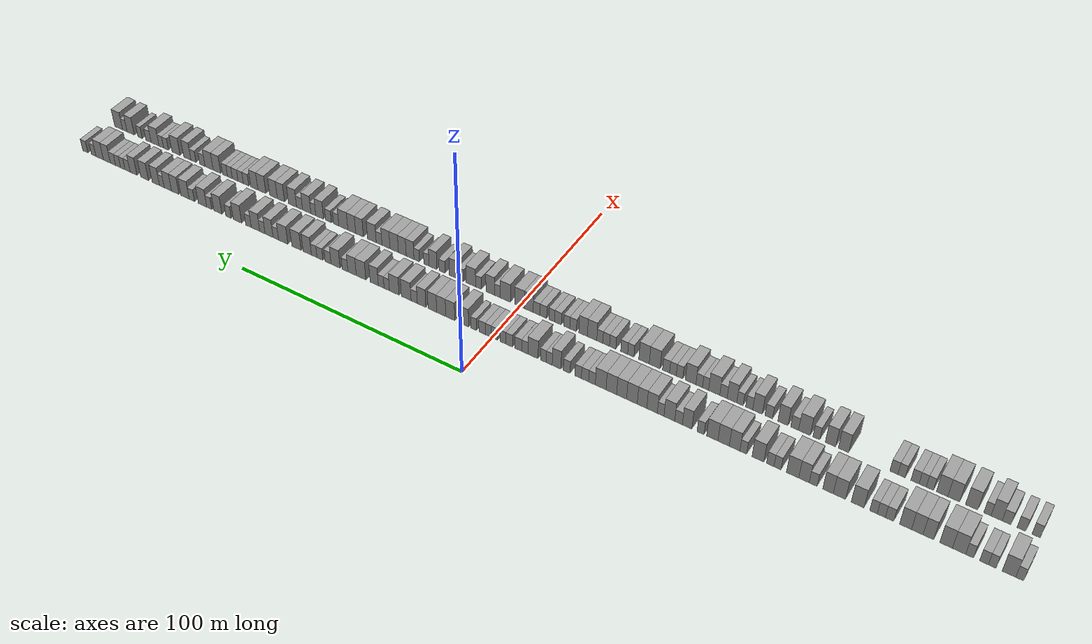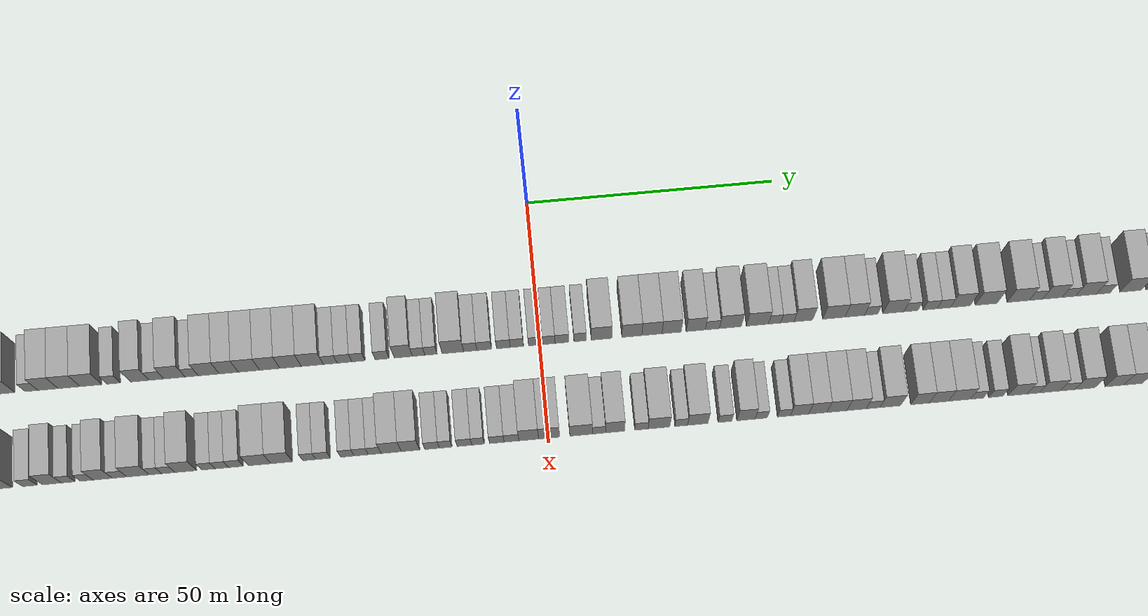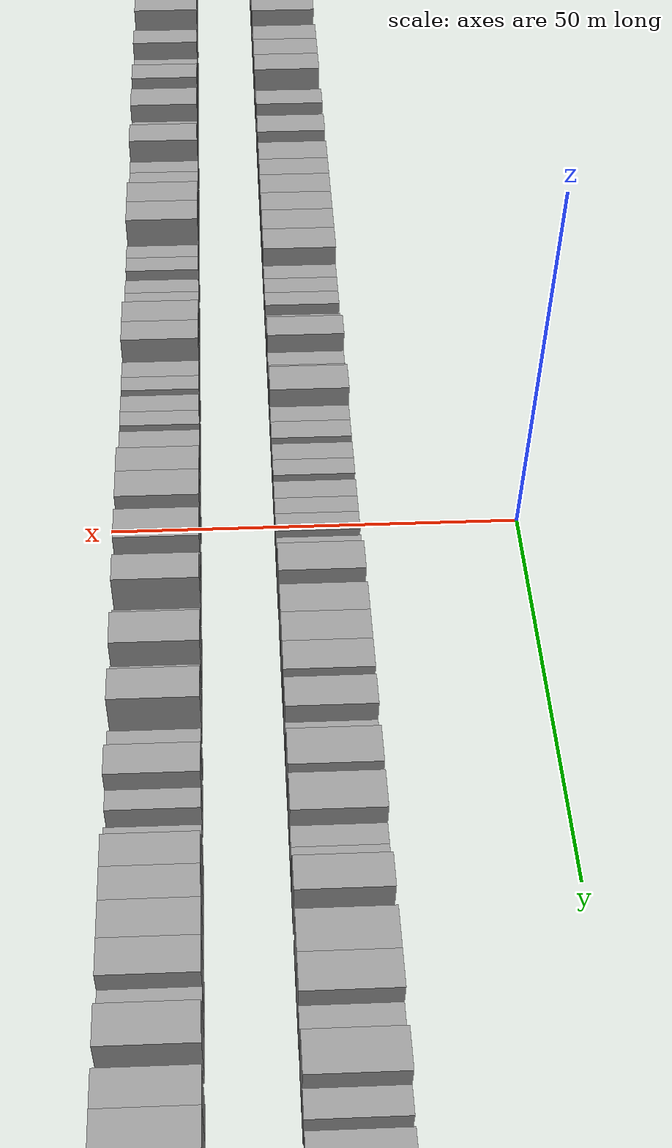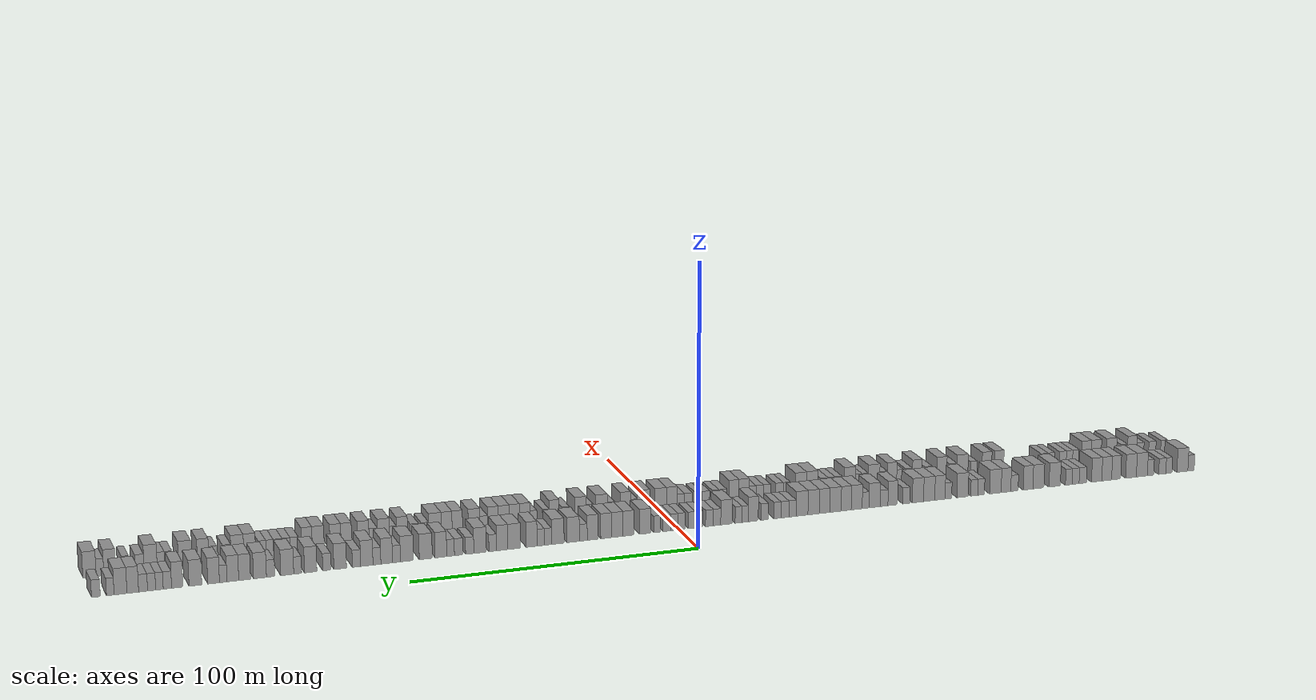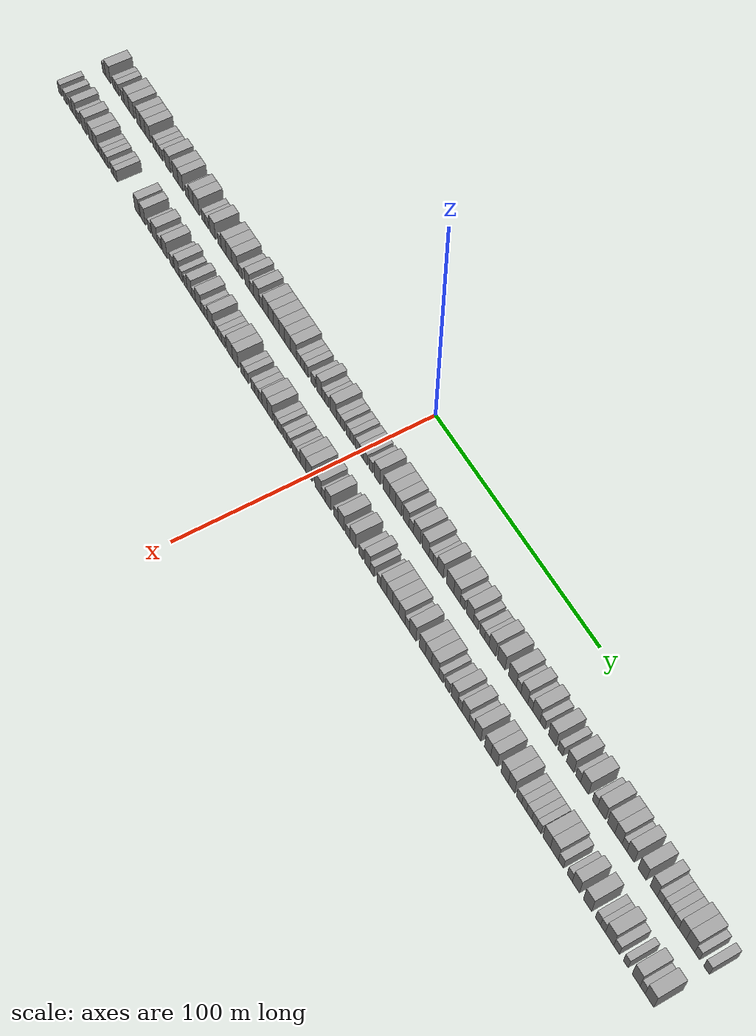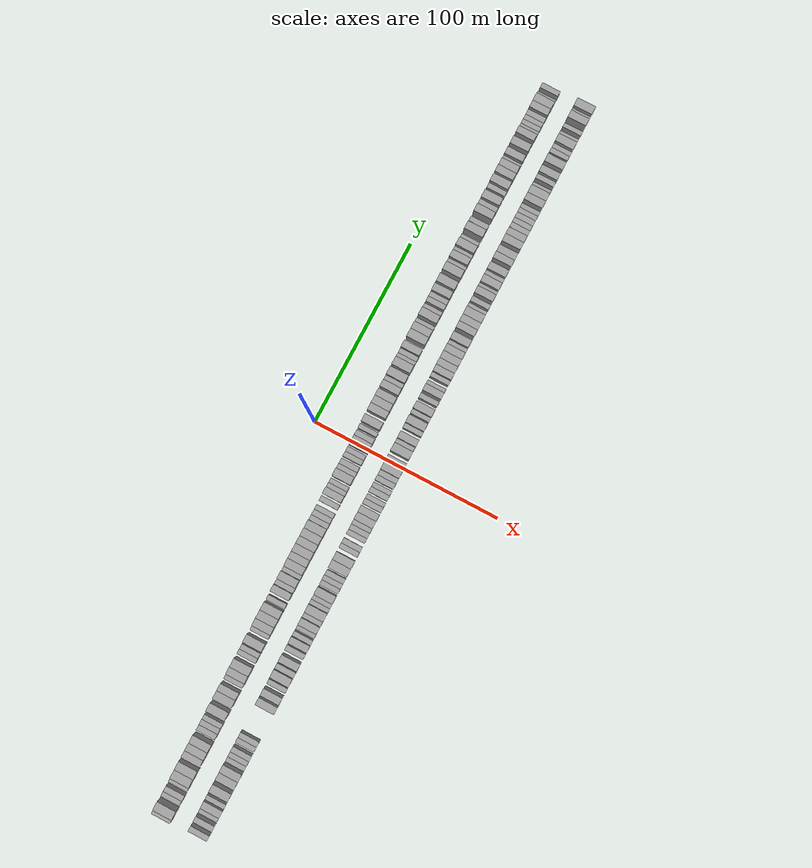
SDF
<sdf version="1.6">
 <world name="default">
  <scene>
   <sky><clouds><speed>12</speed></clouds></sky>
   <ambient>0.4 0.4 0.4 1</ambient>
   <background>0.7 0.7 0.7 1</background>
   <shadows>1</shadows>
  </scene>
  <gravity>0 0 -9.8066</gravity>
  <magnetic_field>6e-06 2.3e-05 -4.2e-05</magnetic_field>
  <physics default="0" name="default_physics" type="ode">
   <ode>
    <solver>
     <type>quick</type>
     <iters>10</iters>
     <sor>1.0</sor>
     <use_dynamic_moi_rescaling>0</use_dynamic_moi_rescaling>
    </solver>
    <constraints>
     <cfm>0</cfm>
     <erp>0.2</erp>
     <contact_max_correcting_vel>100</contact_max_correcting_vel>
     <contact_surface_layer>0.001</contact_surface_layer>
    </constraints>
   </ode>
   <max_step_size>0.004</max_step_size>
   <real_time_factor>1</real_time_factor>
   <real_time_update_rate>250</real_time_update_rate>
  </physics>
  <light name="sun" type="directional">
   <pose>0 0 10 0 0 0</pose>
   <diffuse>0.8 0.8 0.8 1</diffuse>
   <specular>0.2 0.2 0.2 1</specular>
   <attenuation>
    <range>1000</range>
    <constant>0.9</constant>
    <linear>0.01</linear>
    <quadratic>0.001</quadratic>
   </attenuation>
   <direction>-0.5 0.1 -0.9</direction>
  </light>
  <model name="building_1">
   <static>1</static>
   <pose>25.0000 -196.7132 0 0.000000 0.000000 0.000000</pose>
   <link name="link">
    <pose>0 0 3.00 0 0 0</pose>
    <collision name="collision"><geometry><box><size>10.0000 2.5736 6.0000</size></box></geometry></collision>
    <visual name="visual">
     <cast_shadows>0</cast_shadows>
     <geometry><box><size>10.0000 2.5736 6.0000</size></box></geometry>
     <material>
      <script>
       <uri>model://grey_wall/materials/scripts</uri>
       <uri>model://grey_wall/materials/textures</uri>
       <name>vrc/grey_wall</name>
      </script>
     </material>
    </visual>
   </link>
  </model>
  <model name="building_2">
   <static>1</static>
   <pose>25.0000 -193.2047 0 0.000000 0.000000 0.000000</pose>
   <link name="link">
    <pose>0 0 4.50 0 0 0</pose>
    <collision name="collision"><geometry><box><size>10.0000 4.4435 9.0000</size></box></geometry></collision>
    <visual name="visual">
     <cast_shadows>0</cast_shadows>
     <geometry><box><size>10.0000 4.4435 9.0000</size></box></geometry>
     <material>
      <script>
       <uri>model://grey_wall/materials/scripts</uri>
       <uri>model://grey_wall/materials/textures</uri>
       <name>vrc/grey_wall</name>
      </script>
     </material>
    </visual>
   </link>
  </model>
  <model name="building_3">
   <static>1</static>
   <pose>25.0000 -187.7370 0 0.000000 0.000000 0.000000</pose>
   <link name="link">
    <pose>0 0 3.00 0 0 0</pose>
    <collision name="collision"><geometry><box><size>10.0000 2.4917 6.0000</size></box></geometry></collision>
    <visual name="visual">
     <cast_shadows>0</cast_shadows>
     <geometry><box><size>10.0000 2.4917 6.0000</size></box></geometry>
     <material>
      <script>
       <uri>model://grey_wall/materials/scripts</uri>
       <uri>model://grey_wall/materials/textures</uri>
       <name>vrc/grey_wall</name>
      </script>
     </material>
    </visual>
   </link>
  </model>
  <model name="building_4">
   <static>1</static>
   <pose>25.0000 -185.0531 0 0.000000 0.000000 0.000000</pose>
   <link name="link">
    <pose>0 0 3.00 0 0 0</pose>
    <collision name="collision"><geometry><box><size>10.0000 2.8762 6.0000</size></box></geometry></collision>
    <visual name="visual">
     <cast_shadows>0</cast_shadows>
     <geometry><box><size>10.0000 2.8762 6.0000</size></box></geometry>
     <material>
      <script>
       <uri>model://grey_wall/materials/scripts</uri>
       <uri>model://grey_wall/materials/textures</uri>
       <name>vrc/grey_wall</name>
      </script>
     </material>
    </visual>
   </link>
  </model>
  <model name="building_5">
   <static>1</static>
   <pose>25.0000 -180.3151 0 0.000000 0.000000 0.000000</pose>
   <link name="link">
    <pose>0 0 3.00 0 0 0</pose>
    <collision name="collision"><geometry><box><size>10.0000 2.5999 6.0000</size></box></geometry></collision>
    <visual name="visual">
     <cast_shadows>0</cast_shadows>
     <geometry><box><size>10.0000 2.5999 6.0000</size></box></geometry>
     <material>
      <script>
       <uri>model://grey_wall/materials/scripts</uri>
       <uri>model://grey_wall/materials/textures</uri>
       <name>vrc/grey_wall</name>
      </script>
     </material>
    </visual>
   </link>
  </model>
  <model name="building_6">
   <static>1</static>
   <pose>25.0000 -176.8122 0 0.000000 0.000000 0.000000</pose>
   <link name="link">
    <pose>0 0 4.50 0 0 0</pose>
    <collision name="collision"><geometry><box><size>10.0000 4.4058 9.0000</size></box></geometry></collision>
    <visual name="visual">
     <cast_shadows>0</cast_shadows>
     <geometry><box><size>10.0000 4.4058 9.0000</size></box></geometry>
     <material>
      <script>
       <uri>model://grey_wall/materials/scripts</uri>
       <uri>model://grey_wall/materials/textures</uri>
       <name>vrc/grey_wall</name>
      </script>
     </material>
    </visual>
   </link>
  </model>
  <model name="building_7">
   <static>1</static>
   <pose>25.0000 -172.4604 0 0.000000 0.000000 0.000000</pose>
   <link name="link">
    <pose>0 0 4.50 0 0 0</pose>
    <collision name="collision"><geometry><box><size>10.0000 4.2978 9.0000</size></box></geometry></collision>
    <visual name="visual">
     <cast_shadows>0</cast_shadows>
     <geometry><box><size>10.0000 4.2978 9.0000</size></box></geometry>
     <material>
      <script>
       <uri>model://grey_wall/materials/scripts</uri>
       <uri>model://grey_wall/materials/textures</uri>
       <name>vrc/grey_wall</name>
      </script>
     </material>
    </visual>
   </link>
  </model>
  <model name="building_8">
   <static>1</static>
   <pose>25.0000 -166.5079 0 0.000000 0.000000 0.000000</pose>
   <link name="link">
    <pose>0 0 4.50 0 0 0</pose>
    <collision name="collision"><geometry><box><size>10.0000 3.6071 9.0000</size></box></geometry></collision>
    <visual name="visual">
     <cast_shadows>0</cast_shadows>
     <geometry><box><size>10.0000 3.6071 9.0000</size></box></geometry>
     <material>
      <script>
       <uri>model://grey_wall/materials/scripts</uri>
       <uri>model://grey_wall/materials/textures</uri>
       <name>vrc/grey_wall</name>
      </script>
     </material>
    </visual>
   </link>
  </model>
  <model name="building_9">
   <static>1</static>
   <pose>25.0000 -162.7397 0 0.000000 0.000000 0.000000</pose>
   <link name="link">
    <pose>0 0 4.50 0 0 0</pose>
    <collision name="collision"><geometry><box><size>10.0000 3.9293 9.0000</size></box></geometry></collision>
    <visual name="visual">
     <cast_shadows>0</cast_shadows>
     <geometry><box><size>10.0000 3.9293 9.0000</size></box></geometry>
     <material>
      <script>
       <uri>model://grey_wall/materials/scripts</uri>
       <uri>model://grey_wall/materials/textures</uri>
       <name>vrc/grey_wall</name>
      </script>
     </material>
    </visual>
   </link>
  </model>
  <model name="building_10">
   <static>1</static>
   <pose>25.0000 -158.7315 0 0.000000 0.000000 0.000000</pose>
   <link name="link">
    <pose>0 0 4.50 0 0 0</pose>
    <collision name="collision"><geometry><box><size>10.0000 4.0873 9.0000</size></box></geometry></collision>
    <visual name="visual">
     <cast_shadows>0</cast_shadows>
     <geometry><box><size>10.0000 4.0873 9.0000</size></box></geometry>
     <material>
      <script>
       <uri>model://grey_wall/materials/scripts</uri>
       <uri>model://grey_wall/materials/textures</uri>
       <name>vrc/grey_wall</name>
      </script>
     </material>
    </visual>
   </link>
  </model>
  <model name="building_11">
   <static>1</static>
   <pose>25.0000 -153.2360 0 0.000000 0.000000 0.000000</pose>
   <link name="link">
    <pose>0 0 3.00 0 0 0</pose>
    <collision name="collision"><geometry><box><size>10.0000 2.9037 6.0000</size></box></geometry></collision>
    <visual name="visual">
     <cast_shadows>0</cast_shadows>
     <geometry><box><size>10.0000 2.9037 6.0000</size></box></geometry>
     <material>
      <script>
       <uri>model://grey_wall/materials/scripts</uri>
       <uri>model://grey_wall/materials/textures</uri>
       <name>vrc/grey_wall</name>
      </script>
     </material>
    </visual>
   </link>
  </model>
  <model name="building_12">
   <static>1</static>
   <pose>25.0000 -150.3929 0 0.000000 0.000000 0.000000</pose>
   <link name="link">
    <pose>0 0 3.00 0 0 0</pose>
    <collision name="collision"><geometry><box><size>10.0000 2.7824 6.0000</size></box></geometry></collision>
    <visual name="visual">
     <cast_shadows>0</cast_shadows>
     <geometry><box><size>10.0000 2.7824 6.0000</size></box></geometry>
     <material>
      <script>
       <uri>model://grey_wall/materials/scripts</uri>
       <uri>model://grey_wall/materials/textures</uri>
       <name>vrc/grey_wall</name>
      </script>
     </material>
    </visual>
   </link>
  </model>
  <model name="building_13">
   <static>1</static>
   <pose>25.0000 -147.6859 0 0.000000 0.000000 0.000000</pose>
   <link name="link">
    <pose>0 0 3.00 0 0 0</pose>
    <collision name="collision"><geometry><box><size>10.0000 2.6316 6.0000</size></box></geometry></collision>
    <visual name="visual">
     <cast_shadows>0</cast_shadows>
     <geometry><box><size>10.0000 2.6316 6.0000</size></box></geometry>
     <material>
      <script>
       <uri>model://grey_wall/materials/scripts</uri>
       <uri>model://grey_wall/materials/textures</uri>
       <name>vrc/grey_wall</name>
      </script>
     </material>
    </visual>
   </link>
  </model>
  <model name="building_14">
   <static>1</static>
   <pose>25.0000 -142.1304 0 0.000000 0.000000 0.000000</pose>
   <link name="link">
    <pose>0 0 4.50 0 0 0</pose>
    <collision name="collision"><geometry><box><size>10.0000 4.4795 9.0000</size></box></geometry></collision>
    <visual name="visual">
     <cast_shadows>0</cast_shadows>
     <geometry><box><size>10.0000 4.4795 9.0000</size></box></geometry>
     <material>
      <script>
       <uri>model://grey_wall/materials/scripts</uri>
       <uri>model://grey_wall/materials/textures</uri>
       <name>vrc/grey_wall</name>
      </script>
     </material>
    </visual>
   </link>
  </model>
  <model name="building_15">
   <static>1</static>
   <pose>25.0000 -135.7081 0 0.000000 0.000000 0.000000</pose>
   <link name="link">
    <pose>0 0 4.50 0 0 0</pose>
    <collision name="collision"><geometry><box><size>10.0000 4.3652 9.0000</size></box></geometry></collision>
    <visual name="visual">
     <cast_shadows>0</cast_shadows>
     <geometry><box><size>10.0000 4.3652 9.0000</size></box></geometry>
     <material>
      <script>
       <uri>model://grey_wall/materials/scripts</uri>
       <uri>model://grey_wall/materials/textures</uri>
       <name>vrc/grey_wall</name>
      </script>
     </material>
    </visual>
   </link>
  </model>
  <model name="building_16">
   <static>1</static>
   <pose>25.0000 -131.6402 0 0.000000 0.000000 0.000000</pose>
   <link name="link">
    <pose>0 0 4.50 0 0 0</pose>
    <collision name="collision"><geometry><box><size>10.0000 3.7705 9.0000</size></box></geometry></collision>
    <visual name="visual">
     <cast_shadows>0</cast_shadows>
     <geometry><box><size>10.0000 3.7705 9.0000</size></box></geometry>
     <material>
      <script>
       <uri>model://grey_wall/materials/scripts</uri>
       <uri>model://grey_wall/materials/textures</uri>
       <name>vrc/grey_wall</name>
      </script>
     </material>
    </visual>
   </link>
  </model>
  <model name="building_17">
   <static>1</static>
   <pose>25.0000 -126.3235 0 0.000000 0.000000 0.000000</pose>
   <link name="link">
    <pose>0 0 3.00 0 0 0</pose>
    <collision name="collision"><geometry><box><size>10.0000 2.8627 6.0000</size></box></geometry></collision>
    <visual name="visual">
     <cast_shadows>0</cast_shadows>
     <geometry><box><size>10.0000 2.8627 6.0000</size></box></geometry>
     <material>
      <script>
       <uri>model://grey_wall/materials/scripts</uri>
       <uri>model://grey_wall/materials/textures</uri>
       <name>vrc/grey_wall</name>
      </script>
     </material>
    </visual>
   </link>
  </model>
  <model name="building_18">
   <static>1</static>
   <pose>25.0000 -123.0128 0 0.000000 0.000000 0.000000</pose>
   <link name="link">
    <pose>0 0 4.50 0 0 0</pose>
    <collision name="collision"><geometry><box><size>10.0000 3.7586 9.0000</size></box></geometry></collision>
    <visual name="visual">
     <cast_shadows>0</cast_shadows>
     <geometry><box><size>10.0000 3.7586 9.0000</size></box></geometry>
     <material>
      <script>
       <uri>model://grey_wall/materials/scripts</uri>
       <uri>model://grey_wall/materials/textures</uri>
       <name>vrc/grey_wall</name>
      </script>
     </material>
    </visual>
   </link>
  </model>
  <model name="building_19">
   <static>1</static>
   <pose>25.0000 -118.8855 0 0.000000 0.000000 0.000000</pose>
   <link name="link">
    <pose>0 0 4.50 0 0 0</pose>
    <collision name="collision"><geometry><box><size>10.0000 4.4960 9.0000</size></box></geometry></collision>
    <visual name="visual">
     <cast_shadows>0</cast_shadows>
     <geometry><box><size>10.0000 4.4960 9.0000</size></box></geometry>
     <material>
      <script>
       <uri>model://grey_wall/materials/scripts</uri>
       <uri>model://grey_wall/materials/textures</uri>
       <name>vrc/grey_wall</name>
      </script>
     </material>
    </visual>
   </link>
  </model>
  <model name="building_20">
   <static>1</static>
   <pose>25.0000 -113.3541 0 0.000000 0.000000 0.000000</pose>
   <link name="link">
    <pose>0 0 3.00 0 0 0</pose>
    <collision name="collision"><geometry><box><size>10.0000 2.5667 6.0000</size></box></geometry></collision>
    <visual name="visual">
     <cast_shadows>0</cast_shadows>
     <geometry><box><size>10.0000 2.5667 6.0000</size></box></geometry>
     <material>
      <script>
       <uri>model://grey_wall/materials/scripts</uri>
       <uri>model://grey_wall/materials/textures</uri>
       <name>vrc/grey_wall</name>
      </script>
     </material>
    </visual>
   </link>
  </model>
  <model name="building_21">
   <static>1</static>
   <pose>25.0000 -110.7072 0 0.000000 0.000000 0.000000</pose>
   <link name="link">
    <pose>0 0 3.00 0 0 0</pose>
    <collision name="collision"><geometry><box><size>10.0000 2.7272 6.0000</size></box></geometry></collision>
    <visual name="visual">
     <cast_shadows>0</cast_shadows>
     <geometry><box><size>10.0000 2.7272 6.0000</size></box></geometry>
     <material>
      <script>
       <uri>model://grey_wall/materials/scripts</uri>
       <uri>model://grey_wall/materials/textures</uri>
       <name>vrc/grey_wall</name>
      </script>
     </material>
    </visual>
   </link>
  </model>
  <model name="building_22">
   <static>1</static>
   <pose>25.0000 -106.1514 0 0.000000 0.000000 0.000000</pose>
   <link name="link">
    <pose>0 0 4.50 0 0 0</pose>
    <collision name="collision"><geometry><box><size>10.0000 4.3845 9.0000</size></box></geometry></collision>
    <visual name="visual">
     <cast_shadows>0</cast_shadows>
     <geometry><box><size>10.0000 4.3845 9.0000</size></box></geometry>
     <material>
      <script>
       <uri>model://grey_wall/materials/scripts</uri>
       <uri>model://grey_wall/materials/textures</uri>
       <name>vrc/grey_wall</name>
      </script>
     </material>
    </visual>
   </link>
  </model>
  <model name="building_23">
   <static>1</static>
   <pose>25.0000 -100.6900 0 0.000000 0.000000 0.000000</pose>
   <link name="link">
    <pose>0 0 3.00 0 0 0</pose>
    <collision name="collision"><geometry><box><size>10.0000 2.5384 6.0000</size></box></geometry></collision>
    <visual name="visual">
     <cast_shadows>0</cast_shadows>
     <geometry><box><size>10.0000 2.5384 6.0000</size></box></geometry>
     <material>
      <script>
       <uri>model://grey_wall/materials/scripts</uri>
       <uri>model://grey_wall/materials/textures</uri>
       <name>vrc/grey_wall</name>
      </script>
     </material>
    </visual>
   </link>
  </model>
  <model name="building_24">
   <static>1</static>
   <pose>25.0000 -97.4387 0 0.000000 0.000000 0.000000</pose>
   <link name="link">
    <pose>0 0 4.50 0 0 0</pose>
    <collision name="collision"><geometry><box><size>10.0000 3.9641 9.0000</size></box></geometry></collision>
    <visual name="visual">
     <cast_shadows>0</cast_shadows>
     <geometry><box><size>10.0000 3.9641 9.0000</size></box></geometry>
     <material>
      <script>
       <uri>model://grey_wall/materials/scripts</uri>
       <uri>model://grey_wall/materials/textures</uri>
       <name>vrc/grey_wall</name>
      </script>
     </material>
    </visual>
   </link>
  </model>
  <model name="building_25">
   <static>1</static>
   <pose>25.0000 -93.3050 0 0.000000 0.000000 0.000000</pose>
   <link name="link">
    <pose>0 0 4.50 0 0 0</pose>
    <collision name="collision"><geometry><box><size>10.0000 4.3034 9.0000</size></box></geometry></collision>
    <visual name="visual">
     <cast_shadows>0</cast_shadows>
     <geometry><box><size>10.0000 4.3034 9.0000</size></box></geometry>
     <material>
      <script>
       <uri>model://grey_wall/materials/scripts</uri>
       <uri>model://grey_wall/materials/textures</uri>
       <name>vrc/grey_wall</name>
      </script>
     </material>
    </visual>
   </link>
  </model>
  <model name="building_26">
   <static>1</static>
   <pose>25.0000 -89.0119 0 0.000000 0.000000 0.000000</pose>
   <link name="link">
    <pose>0 0 4.50 0 0 0</pose>
    <collision name="collision"><geometry><box><size>10.0000 4.2827 9.0000</size></box></geometry></collision>
    <visual name="visual">
     <cast_shadows>0</cast_shadows>
     <geometry><box><size>10.0000 4.2827 9.0000</size></box></geometry>
     <material>
      <script>
       <uri>model://grey_wall/materials/scripts</uri>
       <uri>model://grey_wall/materials/textures</uri>
       <name>vrc/grey_wall</name>
      </script>
     </material>
    </visual>
   </link>
  </model>
  <model name="building_27">
   <static>1</static>
   <pose>25.0000 -84.5455 0 0.000000 0.000000 0.000000</pose>
   <link name="link">
    <pose>0 0 3.00 0 0 0</pose>
    <collision name="collision"><geometry><box><size>10.0000 2.6500 6.0000</size></box></geometry></collision>
    <visual name="visual">
     <cast_shadows>0</cast_shadows>
     <geometry><box><size>10.0000 2.6500 6.0000</size></box></geometry>
     <material>
      <script>
       <uri>model://grey_wall/materials/scripts</uri>
       <uri>model://grey_wall/materials/textures</uri>
       <name>vrc/grey_wall</name>
      </script>
     </material>
    </visual>
   </link>
  </model>
  <model name="building_28">
   <static>1</static>
   <pose>25.0000 -79.3932 0 0.000000 0.000000 0.000000</pose>
   <link name="link">
    <pose>0 0 4.50 0 0 0</pose>
    <collision name="collision"><geometry><box><size>10.0000 3.6547 9.0000</size></box></geometry></collision>
    <visual name="visual">
     <cast_shadows>0</cast_shadows>
     <geometry><box><size>10.0000 3.6547 9.0000</size></box></geometry>
     <material>
      <script>
       <uri>model://grey_wall/materials/scripts</uri>
       <uri>model://grey_wall/materials/textures</uri>
       <name>vrc/grey_wall</name>
      </script>
     </material>
    </visual>
   </link>
  </model>
  <model name="building_29">
   <static>1</static>
   <pose>25.0000 -76.0867 0 0.000000 0.000000 0.000000</pose>
   <link name="link">
    <pose>0 0 3.00 0 0 0</pose>
    <collision name="collision"><geometry><box><size>10.0000 2.9583 6.0000</size></box></geometry></collision>
    <visual name="visual">
     <cast_shadows>0</cast_shadows>
     <geometry><box><size>10.0000 2.9583 6.0000</size></box></geometry>
     <material>
      <script>
       <uri>model://grey_wall/materials/scripts</uri>
       <uri>model://grey_wall/materials/textures</uri>
       <name>vrc/grey_wall</name>
      </script>
     </material>
    </visual>
   </link>
  </model>
  <model name="building_30">
   <static>1</static>
   <pose>25.0000 -72.5102 0 0.000000 0.000000 0.000000</pose>
   <link name="link">
    <pose>0 0 4.50 0 0 0</pose>
    <collision name="collision"><geometry><box><size>10.0000 4.1946 9.0000</size></box></geometry></collision>
    <visual name="visual">
     <cast_shadows>0</cast_shadows>
     <geometry><box><size>10.0000 4.1946 9.0000</size></box></geometry>
     <material>
      <script>
       <uri>model://grey_wall/materials/scripts</uri>
       <uri>model://grey_wall/materials/textures</uri>
       <name>vrc/grey_wall</name>
      </script>
     </material>
    </visual>
   </link>
  </model>
  <model name="building_31">
   <static>1</static>
   <pose>25.0000 -69.1116 0 0.000000 0.000000 0.000000</pose>
   <link name="link">
    <pose>0 0 3.00 0 0 0</pose>
    <collision name="collision"><geometry><box><size>10.0000 2.6026 6.0000</size></box></geometry></collision>
    <visual name="visual">
     <cast_shadows>0</cast_shadows>
     <geometry><box><size>10.0000 2.6026 6.0000</size></box></geometry>
     <material>
      <script>
       <uri>model://grey_wall/materials/scripts</uri>
       <uri>model://grey_wall/materials/textures</uri>
       <name>vrc/grey_wall</name>
      </script>
     </material>
    </visual>
   </link>
  </model>
  <model name="building_32">
   <static>1</static>
   <pose>25.0000 -65.7340 0 0.000000 0.000000 0.000000</pose>
   <link name="link">
    <pose>0 0 4.50 0 0 0</pose>
    <collision name="collision"><geometry><box><size>10.0000 4.1526 9.0000</size></box></geometry></collision>
    <visual name="visual">
     <cast_shadows>0</cast_shadows>
     <geometry><box><size>10.0000 4.1526 9.0000</size></box></geometry>
     <material>
      <script>
       <uri>model://grey_wall/materials/scripts</uri>
       <uri>model://grey_wall/materials/textures</uri>
       <name>vrc/grey_wall</name>
      </script>
     </material>
    </visual>
   </link>
  </model>
  <model name="building_33">
   <static>1</static>
   <pose>25.0000 -61.7794 0 0.000000 0.000000 0.000000</pose>
   <link name="link">
    <pose>0 0 4.50 0 0 0</pose>
    <collision name="collision"><geometry><box><size>10.0000 3.7566 9.0000</size></box></geometry></collision>
    <visual name="visual">
     <cast_shadows>0</cast_shadows>
     <geometry><box><size>10.0000 3.7566 9.0000</size></box></geometry>
     <material>
      <script>
       <uri>model://grey_wall/materials/scripts</uri>
       <uri>model://grey_wall/materials/textures</uri>
       <name>vrc/grey_wall</name>
      </script>
     </material>
    </visual>
   </link>
  </model>
  <model name="building_34">
   <static>1</static>
   <pose>25.0000 -57.7851 0 0.000000 0.000000 0.000000</pose>
   <link name="link">
    <pose>0 0 4.50 0 0 0</pose>
    <collision name="collision"><geometry><box><size>10.0000 4.2321 9.0000</size></box></geometry></collision>
    <visual name="visual">
     <cast_shadows>0</cast_shadows>
     <geometry><box><size>10.0000 4.2321 9.0000</size></box></geometry>
     <material>
      <script>
       <uri>model://grey_wall/materials/scripts</uri>
       <uri>model://grey_wall/materials/textures</uri>
       <name>vrc/grey_wall</name>
      </script>
     </material>
    </visual>
   </link>
  </model>
  <model name="building_35">
   <static>1</static>
   <pose>25.0000 -53.6690 0 0.000000 0.000000 0.000000</pose>
   <link name="link">
    <pose>0 0 4.50 0 0 0</pose>
    <collision name="collision"><geometry><box><size>10.0000 4.0003 9.0000</size></box></geometry></collision>
    <visual name="visual">
     <cast_shadows>0</cast_shadows>
     <geometry><box><size>10.0000 4.0003 9.0000</size></box></geometry>
     <material>
      <script>
       <uri>model://grey_wall/materials/scripts</uri>
       <uri>model://grey_wall/materials/textures</uri>
       <name>vrc/grey_wall</name>
      </script>
     </material>
    </visual>
   </link>
  </model>
  <model name="building_36">
   <static>1</static>
   <pose>25.0000 -49.5500 0 0.000000 0.000000 0.000000</pose>
   <link name="link">
    <pose>0 0 4.50 0 0 0</pose>
    <collision name="collision"><geometry><box><size>10.0000 4.2375 9.0000</size></box></geometry></collision>
    <visual name="visual">
     <cast_shadows>0</cast_shadows>
     <geometry><box><size>10.0000 4.2375 9.0000</size></box></geometry>
     <material>
      <script>
       <uri>model://grey_wall/materials/scripts</uri>
       <uri>model://grey_wall/materials/textures</uri>
       <name>vrc/grey_wall</name>
      </script>
     </material>
    </visual>
   </link>
  </model>
  <model name="building_37">
   <static>1</static>
   <pose>25.0000 -45.2486 0 0.000000 0.000000 0.000000</pose>
   <link name="link">
    <pose>0 0 4.50 0 0 0</pose>
    <collision name="collision"><geometry><box><size>10.0000 4.3654 9.0000</size></box></geometry></collision>
    <visual name="visual">
     <cast_shadows>0</cast_shadows>
     <geometry><box><size>10.0000 4.3654 9.0000</size></box></geometry>
     <material>
      <script>
       <uri>model://grey_wall/materials/scripts</uri>
       <uri>model://grey_wall/materials/textures</uri>
       <name>vrc/grey_wall</name>
      </script>
     </material>
    </visual>
   </link>
  </model>
  <model name="building_38">
   <static>1</static>
   <pose>25.0000 -41.6955 0 0.000000 0.000000 0.000000</pose>
   <link name="link">
    <pose>0 0 3.00 0 0 0</pose>
    <collision name="collision"><geometry><box><size>10.0000 2.7409 6.0000</size></box></geometry></collision>
    <visual name="visual">
     <cast_shadows>0</cast_shadows>
     <geometry><box><size>10.0000 2.7409 6.0000</size></box></geometry>
     <material>
      <script>
       <uri>model://grey_wall/materials/scripts</uri>
       <uri>model://grey_wall/materials/textures</uri>
       <name>vrc/grey_wall</name>
      </script>
     </material>
    </visual>
   </link>
  </model>
  <model name="building_39">
   <static>1</static>
   <pose>25.0000 -38.8572 0 0.000000 0.000000 0.000000</pose>
   <link name="link">
    <pose>0 0 3.00 0 0 0</pose>
    <collision name="collision"><geometry><box><size>10.0000 2.9356 6.0000</size></box></geometry></collision>
    <visual name="visual">
     <cast_shadows>0</cast_shadows>
     <geometry><box><size>10.0000 2.9356 6.0000</size></box></geometry>
     <material>
      <script>
       <uri>model://grey_wall/materials/scripts</uri>
       <uri>model://grey_wall/materials/textures</uri>
       <name>vrc/grey_wall</name>
      </script>
     </material>
    </visual>
   </link>
  </model>
  <model name="building_40">
   <static>1</static>
   <pose>25.0000 -36.0790 0 0.000000 0.000000 0.000000</pose>
   <link name="link">
    <pose>0 0 3.00 0 0 0</pose>
    <collision name="collision"><geometry><box><size>10.0000 2.6208 6.0000</size></box></geometry></collision>
    <visual name="visual">
     <cast_shadows>0</cast_shadows>
     <geometry><box><size>10.0000 2.6208 6.0000</size></box></geometry>
     <material>
      <script>
       <uri>model://grey_wall/materials/scripts</uri>
       <uri>model://grey_wall/materials/textures</uri>
       <name>vrc/grey_wall</name>
      </script>
     </material>
    </visual>
   </link>
  </model>
  <model name="building_41">
   <static>1</static>
   <pose>25.0000 -31.3737 0 0.000000 0.000000 0.000000</pose>
   <link name="link">
    <pose>0 0 3.00 0 0 0</pose>
    <collision name="collision"><geometry><box><size>10.0000 2.7899 6.0000</size></box></geometry></collision>
    <visual name="visual">
     <cast_shadows>0</cast_shadows>
     <geometry><box><size>10.0000 2.7899 6.0000</size></box></geometry>
     <material>
      <script>
       <uri>model://grey_wall/materials/scripts</uri>
       <uri>model://grey_wall/materials/textures</uri>
       <name>vrc/grey_wall</name>
      </script>
     </material>
    </visual>
   </link>
  </model>
  <model name="building_42">
   <static>1</static>
   <pose>25.0000 -27.1665 0 0.000000 0.000000 0.000000</pose>
   <link name="link">
    <pose>0 0 4.50 0 0 0</pose>
    <collision name="collision"><geometry><box><size>10.0000 3.6244 9.0000</size></box></geometry></collision>
    <visual name="visual">
     <cast_shadows>0</cast_shadows>
     <geometry><box><size>10.0000 3.6244 9.0000</size></box></geometry>
     <material>
      <script>
       <uri>model://grey_wall/materials/scripts</uri>
       <uri>model://grey_wall/materials/textures</uri>
       <name>vrc/grey_wall</name>
      </script>
     </material>
    </visual>
   </link>
  </model>
  <model name="building_43">
   <static>1</static>
   <pose>25.0000 -24.1285 0 0.000000 0.000000 0.000000</pose>
   <link name="link">
    <pose>0 0 3.00 0 0 0</pose>
    <collision name="collision"><geometry><box><size>10.0000 2.4518 6.0000</size></box></geometry></collision>
    <visual name="visual">
     <cast_shadows>0</cast_shadows>
     <geometry><box><size>10.0000 2.4518 6.0000</size></box></geometry>
     <material>
      <script>
       <uri>model://grey_wall/materials/scripts</uri>
       <uri>model://grey_wall/materials/textures</uri>
       <name>vrc/grey_wall</name>
      </script>
     </material>
    </visual>
   </link>
  </model>
  <model name="building_44">
   <static>1</static>
   <pose>25.0000 -21.6762 0 0.000000 0.000000 0.000000</pose>
   <link name="link">
    <pose>0 0 3.00 0 0 0</pose>
    <collision name="collision"><geometry><box><size>10.0000 2.4528 6.0000</size></box></geometry></collision>
    <visual name="visual">
     <cast_shadows>0</cast_shadows>
     <geometry><box><size>10.0000 2.4528 6.0000</size></box></geometry>
     <material>
      <script>
       <uri>model://grey_wall/materials/scripts</uri>
       <uri>model://grey_wall/materials/textures</uri>
       <name>vrc/grey_wall</name>
      </script>
     </material>
    </visual>
   </link>
  </model>
  <model name="building_45">
   <static>1</static>
   <pose>25.0000 -17.3049 0 0.000000 0.000000 0.000000</pose>
   <link name="link">
    <pose>0 0 4.50 0 0 0</pose>
    <collision name="collision"><geometry><box><size>10.0000 4.2897 9.0000</size></box></geometry></collision>
    <visual name="visual">
     <cast_shadows>0</cast_shadows>
     <geometry><box><size>10.0000 4.2897 9.0000</size></box></geometry>
     <material>
      <script>
       <uri>model://grey_wall/materials/scripts</uri>
       <uri>model://grey_wall/materials/textures</uri>
       <name>vrc/grey_wall</name>
      </script>
     </material>
    </visual>
   </link>
  </model>
  <model name="building_46">
   <static>1</static>
   <pose>25.0000 -13.8331 0 0.000000 0.000000 0.000000</pose>
   <link name="link">
    <pose>0 0 3.00 0 0 0</pose>
    <collision name="collision"><geometry><box><size>10.0000 2.6541 6.0000</size></box></geometry></collision>
    <visual name="visual">
     <cast_shadows>0</cast_shadows>
     <geometry><box><size>10.0000 2.6541 6.0000</size></box></geometry>
     <material>
      <script>
       <uri>model://grey_wall/materials/scripts</uri>
       <uri>model://grey_wall/materials/textures</uri>
       <name>vrc/grey_wall</name>
      </script>
     </material>
    </visual>
   </link>
  </model>
  <model name="building_47">
   <static>1</static>
   <pose>25.0000 -11.0533 0 0.000000 0.000000 0.000000</pose>
   <link name="link">
    <pose>0 0 3.00 0 0 0</pose>
    <collision name="collision"><geometry><box><size>10.0000 2.9054 6.0000</size></box></geometry></collision>
    <visual name="visual">
     <cast_shadows>0</cast_shadows>
     <geometry><box><size>10.0000 2.9054 6.0000</size></box></geometry>
     <material>
      <script>
       <uri>model://grey_wall/materials/scripts</uri>
       <uri>model://grey_wall/materials/textures</uri>
       <name>vrc/grey_wall</name>
      </script>
     </material>
    </visual>
   </link>
  </model>
  <model name="building_48">
   <static>1</static>
   <pose>25.0000 -7.2363 0 0.000000 0.000000 0.000000</pose>
   <link name="link">
    <pose>0 0 3.00 0 0 0</pose>
    <collision name="collision"><geometry><box><size>10.0000 2.7287 6.0000</size></box></geometry></collision>
    <visual name="visual">
     <cast_shadows>0</cast_shadows>
     <geometry><box><size>10.0000 2.7287 6.0000</size></box></geometry>
     <material>
      <script>
       <uri>model://grey_wall/materials/scripts</uri>
       <uri>model://grey_wall/materials/textures</uri>
       <name>vrc/grey_wall</name>
      </script>
     </material>
    </visual>
   </link>
  </model>
  <model name="building_49">
   <static>1</static>
   <pose>25.0000 -4.5512 0 0.000000 0.000000 0.000000</pose>
   <link name="link">
    <pose>0 0 3.00 0 0 0</pose>
    <collision name="collision"><geometry><box><size>10.0000 2.6413 6.0000</size></box></geometry></collision>
    <visual name="visual">
     <cast_shadows>0</cast_shadows>
     <geometry><box><size>10.0000 2.6413 6.0000</size></box></geometry>
     <material>
      <script>
       <uri>model://grey_wall/materials/scripts</uri>
       <uri>model://grey_wall/materials/textures</uri>
       <name>vrc/grey_wall</name>
      </script>
     </material>
    </visual>
   </link>
  </model>
  <model name="building_50">
   <static>1</static>
   <pose>25.0000 -0.8488 0 0.000000 0.000000 0.000000</pose>
   <link name="link">
    <pose>0 0 3.00 0 0 0</pose>
    <collision name="collision"><geometry><box><size>10.0000 2.7635 6.0000</size></box></geometry></collision>
    <visual name="visual">
     <cast_shadows>0</cast_shadows>
     <geometry><box><size>10.0000 2.7635 6.0000</size></box></geometry>
     <material>
      <script>
       <uri>model://grey_wall/materials/scripts</uri>
       <uri>model://grey_wall/materials/textures</uri>
       <name>vrc/grey_wall</name>
      </script>
     </material>
    </visual>
   </link>
  </model>
  <model name="building_51">
   <static>1</static>
   <pose>25.0000 1.7864 0 0.000000 0.000000 0.000000</pose>
   <link name="link">
    <pose>0 0 3.00 0 0 0</pose>
    <collision name="collision"><geometry><box><size>10.0000 2.5070 6.0000</size></box></geometry></collision>
    <visual name="visual">
     <cast_shadows>0</cast_shadows>
     <geometry><box><size>10.0000 2.5070 6.0000</size></box></geometry>
     <material>
      <script>
       <uri>model://grey_wall/materials/scripts</uri>
       <uri>model://grey_wall/materials/textures</uri>
       <name>vrc/grey_wall</name>
      </script>
     </material>
    </visual>
   </link>
  </model>
  <model name="building_52">
   <static>1</static>
   <pose>25.0000 4.4324 0 0.000000 0.000000 0.000000</pose>
   <link name="link">
    <pose>0 0 3.00 0 0 0</pose>
    <collision name="collision"><geometry><box><size>10.0000 2.7849 6.0000</size></box></geometry></collision>
    <visual name="visual">
     <cast_shadows>0</cast_shadows>
     <geometry><box><size>10.0000 2.7849 6.0000</size></box></geometry>
     <material>
      <script>
       <uri>model://grey_wall/materials/scripts</uri>
       <uri>model://grey_wall/materials/textures</uri>
       <name>vrc/grey_wall</name>
      </script>
     </material>
    </visual>
   </link>
  </model>
  <model name="building_53">
   <static>1</static>
   <pose>25.0000 8.0485 0 0.000000 0.000000 0.000000</pose>
   <link name="link">
    <pose>0 0 3.00 0 0 0</pose>
    <collision name="collision"><geometry><box><size>10.0000 2.4474 6.0000</size></box></geometry></collision>
    <visual name="visual">
     <cast_shadows>0</cast_shadows>
     <geometry><box><size>10.0000 2.4474 6.0000</size></box></geometry>
     <material>
      <script>
       <uri>model://grey_wall/materials/scripts</uri>
       <uri>model://grey_wall/materials/textures</uri>
       <name>vrc/grey_wall</name>
      </script>
     </material>
    </visual>
   </link>
  </model>
  <model name="building_54">
   <static>1</static>
   <pose>25.0000 12.3292 0 0.000000 0.000000 0.000000</pose>
   <link name="link">
    <pose>0 0 4.50 0 0 0</pose>
    <collision name="collision"><geometry><box><size>10.0000 4.1140 9.0000</size></box></geometry></collision>
    <visual name="visual">
     <cast_shadows>0</cast_shadows>
     <geometry><box><size>10.0000 4.1140 9.0000</size></box></geometry>
     <material>
      <script>
       <uri>model://grey_wall/materials/scripts</uri>
       <uri>model://grey_wall/materials/textures</uri>
       <name>vrc/grey_wall</name>
      </script>
     </material>
    </visual>
   </link>
  </model>
  <model name="building_55">
   <static>1</static>
   <pose>25.0000 18.3756 0 0.000000 0.000000 0.000000</pose>
   <link name="link">
    <pose>0 0 4.50 0 0 0</pose>
    <collision name="collision"><geometry><box><size>10.0000 3.9787 9.0000</size></box></geometry></collision>
    <visual name="visual">
     <cast_shadows>0</cast_shadows>
     <geometry><box><size>10.0000 3.9787 9.0000</size></box></geometry>
     <material>
      <script>
       <uri>model://grey_wall/materials/scripts</uri>
       <uri>model://grey_wall/materials/textures</uri>
       <name>vrc/grey_wall</name>
      </script>
     </material>
    </visual>
   </link>
  </model>
  <model name="building_56">
   <static>1</static>
   <pose>25.0000 22.3830 0 0.000000 0.000000 0.000000</pose>
   <link name="link">
    <pose>0 0 4.50 0 0 0</pose>
    <collision name="collision"><geometry><box><size>10.0000 4.0362 9.0000</size></box></geometry></collision>
    <visual name="visual">
     <cast_shadows>0</cast_shadows>
     <geometry><box><size>10.0000 4.0362 9.0000</size></box></geometry>
     <material>
      <script>
       <uri>model://grey_wall/materials/scripts</uri>
       <uri>model://grey_wall/materials/textures</uri>
       <name>vrc/grey_wall</name>
      </script>
     </material>
    </visual>
   </link>
  </model>
  <model name="building_57">
   <static>1</static>
   <pose>25.0000 26.3301 0 0.000000 0.000000 0.000000</pose>
   <link name="link">
    <pose>0 0 4.50 0 0 0</pose>
    <collision name="collision"><geometry><box><size>10.0000 3.8579 9.0000</size></box></geometry></collision>
    <visual name="visual">
     <cast_shadows>0</cast_shadows>
     <geometry><box><size>10.0000 3.8579 9.0000</size></box></geometry>
     <material>
      <script>
       <uri>model://grey_wall/materials/scripts</uri>
       <uri>model://grey_wall/materials/textures</uri>
       <name>vrc/grey_wall</name>
      </script>
     </material>
    </visual>
   </link>
  </model>
  <model name="building_58">
   <static>1</static>
   <pose>25.0000 31.1724 0 0.000000 0.000000 0.000000</pose>
   <link name="link">
    <pose>0 0 4.50 0 0 0</pose>
    <collision name="collision"><geometry><box><size>10.0000 3.8268 9.0000</size></box></geometry></collision>
    <visual name="visual">
     <cast_shadows>0</cast_shadows>
     <geometry><box><size>10.0000 3.8268 9.0000</size></box></geometry>
     <material>
      <script>
       <uri>model://grey_wall/materials/scripts</uri>
       <uri>model://grey_wall/materials/textures</uri>
       <name>vrc/grey_wall</name>
      </script>
     </material>
    </visual>
   </link>
  </model>
  <model name="building_59">
   <static>1</static>
   <pose>25.0000 34.4945 0 0.000000 0.000000 0.000000</pose>
   <link name="link">
    <pose>0 0 3.00 0 0 0</pose>
    <collision name="collision"><geometry><box><size>10.0000 2.8173 6.0000</size></box></geometry></collision>
    <visual name="visual">
     <cast_shadows>0</cast_shadows>
     <geometry><box><size>10.0000 2.8173 6.0000</size></box></geometry>
     <material>
      <script>
       <uri>model://grey_wall/materials/scripts</uri>
       <uri>model://grey_wall/materials/textures</uri>
       <name>vrc/grey_wall</name>
      </script>
     </material>
    </visual>
   </link>
  </model>
  <model name="building_60">
   <static>1</static>
   <pose>25.0000 38.1174 0 0.000000 0.000000 0.000000</pose>
   <link name="link">
    <pose>0 0 4.50 0 0 0</pose>
    <collision name="collision"><geometry><box><size>10.0000 4.4286 9.0000</size></box></geometry></collision>
    <visual name="visual">
     <cast_shadows>0</cast_shadows>
     <geometry><box><size>10.0000 4.4286 9.0000</size></box></geometry>
     <material>
      <script>
       <uri>model://grey_wall/materials/scripts</uri>
       <uri>model://grey_wall/materials/textures</uri>
       <name>vrc/grey_wall</name>
      </script>
     </material>
    </visual>
   </link>
  </model>
  <model name="building_61">
   <static>1</static>
   <pose>25.0000 43.5494 0 0.000000 0.000000 0.000000</pose>
   <link name="link">
    <pose>0 0 4.50 0 0 0</pose>
    <collision name="collision"><geometry><box><size>10.0000 4.4355 9.0000</size></box></geometry></collision>
    <visual name="visual">
     <cast_shadows>0</cast_shadows>
     <geometry><box><size>10.0000 4.4355 9.0000</size></box></geometry>
     <material>
      <script>
       <uri>model://grey_wall/materials/scripts</uri>
       <uri>model://grey_wall/materials/textures</uri>
       <name>vrc/grey_wall</name>
      </script>
     </material>
    </visual>
   </link>
  </model>
  <model name="building_62">
   <static>1</static>
   <pose>25.0000 46.9996 0 0.000000 0.000000 0.000000</pose>
   <link name="link">
    <pose>0 0 3.00 0 0 0</pose>
    <collision name="collision"><geometry><box><size>10.0000 2.4647 6.0000</size></box></geometry></collision>
    <visual name="visual">
     <cast_shadows>0</cast_shadows>
     <geometry><box><size>10.0000 2.4647 6.0000</size></box></geometry>
     <material>
      <script>
       <uri>model://grey_wall/materials/scripts</uri>
       <uri>model://grey_wall/materials/textures</uri>
       <name>vrc/grey_wall</name>
      </script>
     </material>
    </visual>
   </link>
  </model>
  <model name="building_63">
   <static>1</static>
   <pose>25.0000 49.5599 0 0.000000 0.000000 0.000000</pose>
   <link name="link">
    <pose>0 0 3.00 0 0 0</pose>
    <collision name="collision"><geometry><box><size>10.0000 2.6560 6.0000</size></box></geometry></collision>
    <visual name="visual">
     <cast_shadows>0</cast_shadows>
     <geometry><box><size>10.0000 2.6560 6.0000</size></box></geometry>
     <material>
      <script>
       <uri>model://grey_wall/materials/scripts</uri>
       <uri>model://grey_wall/materials/textures</uri>
       <name>vrc/grey_wall</name>
      </script>
     </material>
    </visual>
   </link>
  </model>
  <model name="building_64">
   <static>1</static>
   <pose>25.0000 52.7791 0 0.000000 0.000000 0.000000</pose>
   <link name="link">
    <pose>0 0 4.50 0 0 0</pose>
    <collision name="collision"><geometry><box><size>10.0000 3.7824 9.0000</size></box></geometry></collision>
    <visual name="visual">
     <cast_shadows>0</cast_shadows>
     <geometry><box><size>10.0000 3.7824 9.0000</size></box></geometry>
     <material>
      <script>
       <uri>model://grey_wall/materials/scripts</uri>
       <uri>model://grey_wall/materials/textures</uri>
       <name>vrc/grey_wall</name>
      </script>
     </material>
    </visual>
   </link>
  </model>
  <model name="building_65">
   <static>1</static>
   <pose>25.0000 58.9103 0 0.000000 0.000000 0.000000</pose>
   <link name="link">
    <pose>0 0 4.50 0 0 0</pose>
    <collision name="collision"><geometry><box><size>10.0000 4.4799 9.0000</size></box></geometry></collision>
    <visual name="visual">
     <cast_shadows>0</cast_shadows>
     <geometry><box><size>10.0000 4.4799 9.0000</size></box></geometry>
     <material>
      <script>
       <uri>model://grey_wall/materials/scripts</uri>
       <uri>model://grey_wall/materials/textures</uri>
       <name>vrc/grey_wall</name>
      </script>
     </material>
    </visual>
   </link>
  </model>
  <model name="building_66">
   <static>1</static>
   <pose>25.0000 63.1264 0 0.000000 0.000000 0.000000</pose>
   <link name="link">
    <pose>0 0 4.50 0 0 0</pose>
    <collision name="collision"><geometry><box><size>10.0000 3.9525 9.0000</size></box></geometry></collision>
    <visual name="visual">
     <cast_shadows>0</cast_shadows>
     <geometry><box><size>10.0000 3.9525 9.0000</size></box></geometry>
     <material>
      <script>
       <uri>model://grey_wall/materials/scripts</uri>
       <uri>model://grey_wall/materials/textures</uri>
       <name>vrc/grey_wall</name>
      </script>
     </material>
    </visual>
   </link>
  </model>
  <model name="building_67">
   <static>1</static>
   <pose>25.0000 66.4353 0 0.000000 0.000000 0.000000</pose>
   <link name="link">
    <pose>0 0 3.00 0 0 0</pose>
    <collision name="collision"><geometry><box><size>10.0000 2.6653 6.0000</size></box></geometry></collision>
    <visual name="visual">
     <cast_shadows>0</cast_shadows>
     <geometry><box><size>10.0000 2.6653 6.0000</size></box></geometry>
     <material>
      <script>
       <uri>model://grey_wall/materials/scripts</uri>
       <uri>model://grey_wall/materials/textures</uri>
       <name>vrc/grey_wall</name>
      </script>
     </material>
    </visual>
   </link>
  </model>
  <model name="building_68">
   <static>1</static>
   <pose>25.0000 70.9002 0 0.000000 0.000000 0.000000</pose>
   <link name="link">
    <pose>0 0 4.50 0 0 0</pose>
    <collision name="collision"><geometry><box><size>10.0000 4.2645 9.0000</size></box></geometry></collision>
    <visual name="visual">
     <cast_shadows>0</cast_shadows>
     <geometry><box><size>10.0000 4.2645 9.0000</size></box></geometry>
     <material>
      <script>
       <uri>model://grey_wall/materials/scripts</uri>
       <uri>model://grey_wall/materials/textures</uri>
       <name>vrc/grey_wall</name>
      </script>
     </material>
    </visual>
   </link>
  </model>
  <model name="building_69">
   <static>1</static>
   <pose>25.0000 74.4562 0 0.000000 0.000000 0.000000</pose>
   <link name="link">
    <pose>0 0 3.00 0 0 0</pose>
    <collision name="collision"><geometry><box><size>10.0000 2.8476 6.0000</size></box></geometry></collision>
    <visual name="visual">
     <cast_shadows>0</cast_shadows>
     <geometry><box><size>10.0000 2.8476 6.0000</size></box></geometry>
     <material>
      <script>
       <uri>model://grey_wall/materials/scripts</uri>
       <uri>model://grey_wall/materials/textures</uri>
       <name>vrc/grey_wall</name>
      </script>
     </material>
    </visual>
   </link>
  </model>
  <model name="building_70">
   <static>1</static>
   <pose>25.0000 78.3200 0 0.000000 0.000000 0.000000</pose>
   <link name="link">
    <pose>0 0 3.00 0 0 0</pose>
    <collision name="collision"><geometry><box><size>10.0000 2.8800 6.0000</size></box></geometry></collision>
    <visual name="visual">
     <cast_shadows>0</cast_shadows>
     <geometry><box><size>10.0000 2.8800 6.0000</size></box></geometry>
     <material>
      <script>
       <uri>model://grey_wall/materials/scripts</uri>
       <uri>model://grey_wall/materials/textures</uri>
       <name>vrc/grey_wall</name>
      </script>
     </material>
    </visual>
   </link>
  </model>
  <model name="building_71">
   <static>1</static>
   <pose>25.0000 81.1000 0 0.000000 0.000000 0.000000</pose>
   <link name="link">
    <pose>0 0 3.00 0 0 0</pose>
    <collision name="collision"><geometry><box><size>10.0000 2.6799 6.0000</size></box></geometry></collision>
    <visual name="visual">
     <cast_shadows>0</cast_shadows>
     <geometry><box><size>10.0000 2.6799 6.0000</size></box></geometry>
     <material>
      <script>
       <uri>model://grey_wall/materials/scripts</uri>
       <uri>model://grey_wall/materials/textures</uri>
       <name>vrc/grey_wall</name>
      </script>
     </material>
    </visual>
   </link>
  </model>
  <model name="building_72">
   <static>1</static>
   <pose>25.0000 84.4372 0 0.000000 0.000000 0.000000</pose>
   <link name="link">
    <pose>0 0 4.50 0 0 0</pose>
    <collision name="collision"><geometry><box><size>10.0000 3.9945 9.0000</size></box></geometry></collision>
    <visual name="visual">
     <cast_shadows>0</cast_shadows>
     <geometry><box><size>10.0000 3.9945 9.0000</size></box></geometry>
     <material>
      <script>
       <uri>model://grey_wall/materials/scripts</uri>
       <uri>model://grey_wall/materials/textures</uri>
       <name>vrc/grey_wall</name>
      </script>
     </material>
    </visual>
   </link>
  </model>
  <model name="building_73">
   <static>1</static>
   <pose>25.0000 89.6649 0 0.000000 0.000000 0.000000</pose>
   <link name="link">
    <pose>0 0 4.50 0 0 0</pose>
    <collision name="collision"><geometry><box><size>10.0000 4.4609 9.0000</size></box></geometry></collision>
    <visual name="visual">
     <cast_shadows>0</cast_shadows>
     <geometry><box><size>10.0000 4.4609 9.0000</size></box></geometry>
     <material>
      <script>
       <uri>model://grey_wall/materials/scripts</uri>
       <uri>model://grey_wall/materials/textures</uri>
       <name>vrc/grey_wall</name>
      </script>
     </material>
    </visual>
   </link>
  </model>
  <model name="building_74">
   <static>1</static>
   <pose>25.0000 96.1412 0 0.000000 0.000000 0.000000</pose>
   <link name="link">
    <pose>0 0 4.50 0 0 0</pose>
    <collision name="collision"><geometry><box><size>10.0000 4.4915 9.0000</size></box></geometry></collision>
    <visual name="visual">
     <cast_shadows>0</cast_shadows>
     <geometry><box><size>10.0000 4.4915 9.0000</size></box></geometry>
     <material>
      <script>
       <uri>model://grey_wall/materials/scripts</uri>
       <uri>model://grey_wall/materials/textures</uri>
       <name>vrc/grey_wall</name>
      </script>
     </material>
    </visual>
   </link>
  </model>
  <model name="building_75">
   <static>1</static>
   <pose>25.0000 99.7424 0 0.000000 0.000000 0.000000</pose>
   <link name="link">
    <pose>0 0 3.00 0 0 0</pose>
    <collision name="collision"><geometry><box><size>10.0000 2.7109 6.0000</size></box></geometry></collision>
    <visual name="visual">
     <cast_shadows>0</cast_shadows>
     <geometry><box><size>10.0000 2.7109 6.0000</size></box></geometry>
     <material>
      <script>
       <uri>model://grey_wall/materials/scripts</uri>
       <uri>model://grey_wall/materials/textures</uri>
       <name>vrc/grey_wall</name>
      </script>
     </material>
    </visual>
   </link>
  </model>
  <model name="building_76">
   <static>1</static>
   <pose>25.0000 103.0812 0 0.000000 0.000000 0.000000</pose>
   <link name="link">
    <pose>0 0 4.50 0 0 0</pose>
    <collision name="collision"><geometry><box><size>10.0000 3.9667 9.0000</size></box></geometry></collision>
    <visual name="visual">
     <cast_shadows>0</cast_shadows>
     <geometry><box><size>10.0000 3.9667 9.0000</size></box></geometry>
     <material>
      <script>
       <uri>model://grey_wall/materials/scripts</uri>
       <uri>model://grey_wall/materials/textures</uri>
       <name>vrc/grey_wall</name>
      </script>
     </material>
    </visual>
   </link>
  </model>
  <model name="building_77">
   <static>1</static>
   <pose>25.0000 106.4107 0 0.000000 0.000000 0.000000</pose>
   <link name="link">
    <pose>0 0 3.00 0 0 0</pose>
    <collision name="collision"><geometry><box><size>10.0000 2.6924 6.0000</size></box></geometry></collision>
    <visual name="visual">
     <cast_shadows>0</cast_shadows>
     <geometry><box><size>10.0000 2.6924 6.0000</size></box></geometry>
     <material>
      <script>
       <uri>model://grey_wall/materials/scripts</uri>
       <uri>model://grey_wall/materials/textures</uri>
       <name>vrc/grey_wall</name>
      </script>
     </material>
    </visual>
   </link>
  </model>
  <model name="building_78">
   <static>1</static>
   <pose>25.0000 109.8622 0 0.000000 0.000000 0.000000</pose>
   <link name="link">
    <pose>0 0 4.50 0 0 0</pose>
    <collision name="collision"><geometry><box><size>10.0000 4.2106 9.0000</size></box></geometry></collision>
    <visual name="visual">
     <cast_shadows>0</cast_shadows>
     <geometry><box><size>10.0000 4.2106 9.0000</size></box></geometry>
     <material>
      <script>
       <uri>model://grey_wall/materials/scripts</uri>
       <uri>model://grey_wall/materials/textures</uri>
       <name>vrc/grey_wall</name>
      </script>
     </material>
    </visual>
   </link>
  </model>
  <model name="building_79">
   <static>1</static>
   <pose>25.0000 113.3629 0 0.000000 0.000000 0.000000</pose>
   <link name="link">
    <pose>0 0 3.00 0 0 0</pose>
    <collision name="collision"><geometry><box><size>10.0000 2.7908 6.0000</size></box></geometry></collision>
    <visual name="visual">
     <cast_shadows>0</cast_shadows>
     <geometry><box><size>10.0000 2.7908 6.0000</size></box></geometry>
     <material>
      <script>
       <uri>model://grey_wall/materials/scripts</uri>
       <uri>model://grey_wall/materials/textures</uri>
       <name>vrc/grey_wall</name>
      </script>
     </material>
    </visual>
   </link>
  </model>
  <model name="building_80">
   <static>1</static>
   <pose>25.0000 118.8884 0 0.000000 0.000000 0.000000</pose>
   <link name="link">
    <pose>0 0 4.50 0 0 0</pose>
    <collision name="collision"><geometry><box><size>10.0000 4.2603 9.0000</size></box></geometry></collision>
    <visual name="visual">
     <cast_shadows>0</cast_shadows>
     <geometry><box><size>10.0000 4.2603 9.0000</size></box></geometry>
     <material>
      <script>
       <uri>model://grey_wall/materials/scripts</uri>
       <uri>model://grey_wall/materials/textures</uri>
       <name>vrc/grey_wall</name>
      </script>
     </material>
    </visual>
   </link>
  </model>
  <model name="building_81">
   <static>1</static>
   <pose>25.0000 123.3897 0 0.000000 0.000000 0.000000</pose>
   <link name="link">
    <pose>0 0 3.00 0 0 0</pose>
    <collision name="collision"><geometry><box><size>10.0000 2.7422 6.0000</size></box></geometry></collision>
    <visual name="visual">
     <cast_shadows>0</cast_shadows>
     <geometry><box><size>10.0000 2.7422 6.0000</size></box></geometry>
     <material>
      <script>
       <uri>model://grey_wall/materials/scripts</uri>
       <uri>model://grey_wall/materials/textures</uri>
       <name>vrc/grey_wall</name>
      </script>
     </material>
    </visual>
   </link>
  </model>
  <model name="building_82">
   <static>1</static>
   <pose>25.0000 128.8317 0 0.000000 0.000000 0.000000</pose>
   <link name="link">
    <pose>0 0 4.50 0 0 0</pose>
    <collision name="collision"><geometry><box><size>10.0000 4.1418 9.0000</size></box></geometry></collision>
    <visual name="visual">
     <cast_shadows>0</cast_shadows>
     <geometry><box><size>10.0000 4.1418 9.0000</size></box></geometry>
     <material>
      <script>
       <uri>model://grey_wall/materials/scripts</uri>
       <uri>model://grey_wall/materials/textures</uri>
       <name>vrc/grey_wall</name>
      </script>
     </material>
    </visual>
   </link>
  </model>
  <model name="building_83">
   <static>1</static>
   <pose>25.0000 133.2187 0 0.000000 0.000000 0.000000</pose>
   <link name="link">
    <pose>0 0 3.00 0 0 0</pose>
    <collision name="collision"><geometry><box><size>10.0000 2.6321 6.0000</size></box></geometry></collision>
    <visual name="visual">
     <cast_shadows>0</cast_shadows>
     <geometry><box><size>10.0000 2.6321 6.0000</size></box></geometry>
     <material>
      <script>
       <uri>model://grey_wall/materials/scripts</uri>
       <uri>model://grey_wall/materials/textures</uri>
       <name>vrc/grey_wall</name>
      </script>
     </material>
    </visual>
   </link>
  </model>
  <model name="building_84">
   <static>1</static>
   <pose>25.0000 136.7079 0 0.000000 0.000000 0.000000</pose>
   <link name="link">
    <pose>0 0 4.50 0 0 0</pose>
    <collision name="collision"><geometry><box><size>10.0000 4.3463 9.0000</size></box></geometry></collision>
    <visual name="visual">
     <cast_shadows>0</cast_shadows>
     <geometry><box><size>10.0000 4.3463 9.0000</size></box></geometry>
     <material>
      <script>
       <uri>model://grey_wall/materials/scripts</uri>
       <uri>model://grey_wall/materials/textures</uri>
       <name>vrc/grey_wall</name>
      </script>
     </material>
    </visual>
   </link>
  </model>
  <model name="building_85">
   <static>1</static>
   <pose>25.0000 142.2719 0 0.000000 0.000000 0.000000</pose>
   <link name="link">
    <pose>0 0 3.00 0 0 0</pose>
    <collision name="collision"><geometry><box><size>10.0000 2.7816 6.0000</size></box></geometry></collision>
    <visual name="visual">
     <cast_shadows>0</cast_shadows>
     <geometry><box><size>10.0000 2.7816 6.0000</size></box></geometry>
     <material>
      <script>
       <uri>model://grey_wall/materials/scripts</uri>
       <uri>model://grey_wall/materials/textures</uri>
       <name>vrc/grey_wall</name>
      </script>
     </material>
    </visual>
   </link>
  </model>
  <model name="building_86">
   <static>1</static>
   <pose>25.0000 145.8068 0 0.000000 0.000000 0.000000</pose>
   <link name="link">
    <pose>0 0 4.50 0 0 0</pose>
    <collision name="collision"><geometry><box><size>10.0000 4.2884 9.0000</size></box></geometry></collision>
    <visual name="visual">
     <cast_shadows>0</cast_shadows>
     <geometry><box><size>10.0000 4.2884 9.0000</size></box></geometry>
     <material>
      <script>
       <uri>model://grey_wall/materials/scripts</uri>
       <uri>model://grey_wall/materials/textures</uri>
       <name>vrc/grey_wall</name>
      </script>
     </material>
    </visual>
   </link>
  </model>
  <model name="building_87">
   <static>1</static>
   <pose>25.0000 150.9141 0 0.000000 0.000000 0.000000</pose>
   <link name="link">
    <pose>0 0 4.50 0 0 0</pose>
    <collision name="collision"><geometry><box><size>10.0000 3.9263 9.0000</size></box></geometry></collision>
    <visual name="visual">
     <cast_shadows>0</cast_shadows>
     <geometry><box><size>10.0000 3.9263 9.0000</size></box></geometry>
     <material>
      <script>
       <uri>model://grey_wall/materials/scripts</uri>
       <uri>model://grey_wall/materials/textures</uri>
       <name>vrc/grey_wall</name>
      </script>
     </material>
    </visual>
   </link>
  </model>
  <model name="building_88">
   <static>1</static>
   <pose>25.0000 154.8067 0 0.000000 0.000000 0.000000</pose>
   <link name="link">
    <pose>0 0 4.50 0 0 0</pose>
    <collision name="collision"><geometry><box><size>10.0000 3.8588 9.0000</size></box></geometry></collision>
    <visual name="visual">
     <cast_shadows>0</cast_shadows>
     <geometry><box><size>10.0000 3.8588 9.0000</size></box></geometry>
     <material>
      <script>
       <uri>model://grey_wall/materials/scripts</uri>
       <uri>model://grey_wall/materials/textures</uri>
       <name>vrc/grey_wall</name>
      </script>
     </material>
    </visual>
   </link>
  </model>
  <model name="building_89">
   <static>1</static>
   <pose>25.0000 157.9912 0 0.000000 0.000000 0.000000</pose>
   <link name="link">
    <pose>0 0 3.00 0 0 0</pose>
    <collision name="collision"><geometry><box><size>10.0000 2.5101 6.0000</size></box></geometry></collision>
    <visual name="visual">
     <cast_shadows>0</cast_shadows>
     <geometry><box><size>10.0000 2.5101 6.0000</size></box></geometry>
     <material>
      <script>
       <uri>model://grey_wall/materials/scripts</uri>
       <uri>model://grey_wall/materials/textures</uri>
       <name>vrc/grey_wall</name>
      </script>
     </material>
    </visual>
   </link>
  </model>
  <model name="building_90">
   <static>1</static>
   <pose>25.0000 161.1635 0 0.000000 0.000000 0.000000</pose>
   <link name="link">
    <pose>0 0 4.50 0 0 0</pose>
    <collision name="collision"><geometry><box><size>10.0000 3.8345 9.0000</size></box></geometry></collision>
    <visual name="visual">
     <cast_shadows>0</cast_shadows>
     <geometry><box><size>10.0000 3.8345 9.0000</size></box></geometry>
     <material>
      <script>
       <uri>model://grey_wall/materials/scripts</uri>
       <uri>model://grey_wall/materials/textures</uri>
       <name>vrc/grey_wall</name>
      </script>
     </material>
    </visual>
   </link>
  </model>
  <model name="building_91">
   <static>1</static>
   <pose>25.0000 167.1730 0 0.000000 0.000000 0.000000</pose>
   <link name="link">
    <pose>0 0 4.50 0 0 0</pose>
    <collision name="collision"><geometry><box><size>10.0000 4.1845 9.0000</size></box></geometry></collision>
    <visual name="visual">
     <cast_shadows>0</cast_shadows>
     <geometry><box><size>10.0000 4.1845 9.0000</size></box></geometry>
     <material>
      <script>
       <uri>model://grey_wall/materials/scripts</uri>
       <uri>model://grey_wall/materials/textures</uri>
       <name>vrc/grey_wall</name>
      </script>
     </material>
    </visual>
   </link>
  </model>
  <model name="building_92">
   <static>1</static>
   <pose>25.0000 173.1175 0 0.000000 0.000000 0.000000</pose>
   <link name="link">
    <pose>0 0 4.50 0 0 0</pose>
    <collision name="collision"><geometry><box><size>10.0000 3.7043 9.0000</size></box></geometry></collision>
    <visual name="visual">
     <cast_shadows>0</cast_shadows>
     <geometry><box><size>10.0000 3.7043 9.0000</size></box></geometry>
     <material>
      <script>
       <uri>model://grey_wall/materials/scripts</uri>
       <uri>model://grey_wall/materials/textures</uri>
       <name>vrc/grey_wall</name>
      </script>
     </material>
    </visual>
   </link>
  </model>
  <model name="building_93">
   <static>1</static>
   <pose>25.0000 176.3418 0 0.000000 0.000000 0.000000</pose>
   <link name="link">
    <pose>0 0 3.00 0 0 0</pose>
    <collision name="collision"><geometry><box><size>10.0000 2.7443 6.0000</size></box></geometry></collision>
    <visual name="visual">
     <cast_shadows>0</cast_shadows>
     <geometry><box><size>10.0000 2.7443 6.0000</size></box></geometry>
     <material>
      <script>
       <uri>model://grey_wall/materials/scripts</uri>
       <uri>model://grey_wall/materials/textures</uri>
       <name>vrc/grey_wall</name>
      </script>
     </material>
    </visual>
   </link>
  </model>
  <model name="building_94">
   <static>1</static>
   <pose>25.0000 178.9468 0 0.000000 0.000000 0.000000</pose>
   <link name="link">
    <pose>0 0 3.00 0 0 0</pose>
    <collision name="collision"><geometry><box><size>10.0000 2.4656 6.0000</size></box></geometry></collision>
    <visual name="visual">
     <cast_shadows>0</cast_shadows>
     <geometry><box><size>10.0000 2.4656 6.0000</size></box></geometry>
     <material>
      <script>
       <uri>model://grey_wall/materials/scripts</uri>
       <uri>model://grey_wall/materials/textures</uri>
       <name>vrc/grey_wall</name>
      </script>
     </material>
    </visual>
   </link>
  </model>
  <model name="building_95">
   <static>1</static>
   <pose>25.0000 181.4987 0 0.000000 0.000000 0.000000</pose>
   <link name="link">
    <pose>0 0 3.00 0 0 0</pose>
    <collision name="collision"><geometry><box><size>10.0000 2.6382 6.0000</size></box></geometry></collision>
    <visual name="visual">
     <cast_shadows>0</cast_shadows>
     <geometry><box><size>10.0000 2.6382 6.0000</size></box></geometry>
     <material>
      <script>
       <uri>model://grey_wall/materials/scripts</uri>
       <uri>model://grey_wall/materials/textures</uri>
       <name>vrc/grey_wall</name>
      </script>
     </material>
    </visual>
   </link>
  </model>
  <model name="building_96">
   <static>1</static>
   <pose>25.0000 184.2789 0 0.000000 0.000000 0.000000</pose>
   <link name="link">
    <pose>0 0 3.00 0 0 0</pose>
    <collision name="collision"><geometry><box><size>10.0000 2.9223 6.0000</size></box></geometry></collision>
    <visual name="visual">
     <cast_shadows>0</cast_shadows>
     <geometry><box><size>10.0000 2.9223 6.0000</size></box></geometry>
     <material>
      <script>
       <uri>model://grey_wall/materials/scripts</uri>
       <uri>model://grey_wall/materials/textures</uri>
       <name>vrc/grey_wall</name>
      </script>
     </material>
    </visual>
   </link>
  </model>
  <model name="building_97">
   <static>1</static>
   <pose>25.0000 187.6226 0 0.000000 0.000000 0.000000</pose>
   <link name="link">
    <pose>0 0 4.50 0 0 0</pose>
    <collision name="collision"><geometry><box><size>10.0000 3.7651 9.0000</size></box></geometry></collision>
    <visual name="visual">
     <cast_shadows>0</cast_shadows>
     <geometry><box><size>10.0000 3.7651 9.0000</size></box></geometry>
     <material>
      <script>
       <uri>model://grey_wall/materials/scripts</uri>
       <uri>model://grey_wall/materials/textures</uri>
       <name>vrc/grey_wall</name>
      </script>
     </material>
    </visual>
   </link>
  </model>
  <model name="building_98">
   <static>1</static>
   <pose>25.0000 191.5946 0 0.000000 0.000000 0.000000</pose>
   <link name="link">
    <pose>0 0 4.50 0 0 0</pose>
    <collision name="collision"><geometry><box><size>10.0000 4.1790 9.0000</size></box></geometry></collision>
    <visual name="visual">
     <cast_shadows>0</cast_shadows>
     <geometry><box><size>10.0000 4.1790 9.0000</size></box></geometry>
     <material>
      <script>
       <uri>model://grey_wall/materials/scripts</uri>
       <uri>model://grey_wall/materials/textures</uri>
       <name>vrc/grey_wall</name>
      </script>
     </material>
    </visual>
   </link>
  </model>
  <model name="building_99">
   <static>1</static>
   <pose>25.0000 194.9133 0 0.000000 0.000000 0.000000</pose>
   <link name="link">
    <pose>0 0 3.00 0 0 0</pose>
    <collision name="collision"><geometry><box><size>10.0000 2.4584 6.0000</size></box></geometry></collision>
    <visual name="visual">
     <cast_shadows>0</cast_shadows>
     <geometry><box><size>10.0000 2.4584 6.0000</size></box></geometry>
     <material>
      <script>
       <uri>model://grey_wall/materials/scripts</uri>
       <uri>model://grey_wall/materials/textures</uri>
       <name>vrc/grey_wall</name>
      </script>
     </material>
    </visual>
   </link>
  </model>
  <model name="building_100">
   <static>1</static>
   <pose>25.0000 199.5589 0 0.000000 0.000000 0.000000</pose>
   <link name="link">
    <pose>0 0 3.00 0 0 0</pose>
    <collision name="collision"><geometry><box><size>10.0000 2.8327 6.0000</size></box></geometry></collision>
    <visual name="visual">
     <cast_shadows>0</cast_shadows>
     <geometry><box><size>10.0000 2.8327 6.0000</size></box></geometry>
     <material>
      <script>
       <uri>model://grey_wall/materials/scripts</uri>
       <uri>model://grey_wall/materials/textures</uri>
       <name>vrc/grey_wall</name>
      </script>
     </material>
    </visual>
   </link>
  </model>
  <model name="building_101">
   <static>1</static>
   <pose>44.0000 -195.6258 0 0.000000 0.000000 0.000000</pose>
   <link name="link">
    <pose>0 0 3.00 0 0 0</pose>
    <collision name="collision"><geometry><box><size>10.0000 2.7484 6.0000</size></box></geometry></collision>
    <visual name="visual">
     <cast_shadows>0</cast_shadows>
     <geometry><box><size>10.0000 2.7484 6.0000</size></box></geometry>
     <material>
      <script>
       <uri>model://grey_wall/materials/scripts</uri>
       <uri>model://grey_wall/materials/textures</uri>
       <name>vrc/grey_wall</name>
      </script>
     </material>
    </visual>
   </link>
  </model>
  <model name="building_102">
   <static>1</static>
   <pose>44.0000 -190.7808 0 0.000000 0.000000 0.000000</pose>
   <link name="link">
    <pose>0 0 3.00 0 0 0</pose>
    <collision name="collision"><geometry><box><size>10.0000 2.9414 6.0000</size></box></geometry></collision>
    <visual name="visual">
     <cast_shadows>0</cast_shadows>
     <geometry><box><size>10.0000 2.9414 6.0000</size></box></geometry>
     <material>
      <script>
       <uri>model://grey_wall/materials/scripts</uri>
       <uri>model://grey_wall/materials/textures</uri>
       <name>vrc/grey_wall</name>
      </script>
     </material>
    </visual>
   </link>
  </model>
  <model name="building_103">
   <static>1</static>
   <pose>44.0000 -185.8272 0 0.000000 0.000000 0.000000</pose>
   <link name="link">
    <pose>0 0 3.00 0 0 0</pose>
    <collision name="collision"><geometry><box><size>10.0000 2.9658 6.0000</size></box></geometry></collision>
    <visual name="visual">
     <cast_shadows>0</cast_shadows>
     <geometry><box><size>10.0000 2.9658 6.0000</size></box></geometry>
     <material>
      <script>
       <uri>model://grey_wall/materials/scripts</uri>
       <uri>model://grey_wall/materials/textures</uri>
       <name>vrc/grey_wall</name>
      </script>
     </material>
    </visual>
   </link>
  </model>
  <model name="building_104">
   <static>1</static>
   <pose>44.0000 -182.4751 0 0.000000 0.000000 0.000000</pose>
   <link name="link">
    <pose>0 0 4.50 0 0 0</pose>
    <collision name="collision"><geometry><box><size>10.0000 3.7385 9.0000</size></box></geometry></collision>
    <visual name="visual">
     <cast_shadows>0</cast_shadows>
     <geometry><box><size>10.0000 3.7385 9.0000</size></box></geometry>
     <material>
      <script>
       <uri>model://grey_wall/materials/scripts</uri>
       <uri>model://grey_wall/materials/textures</uri>
       <name>vrc/grey_wall</name>
      </script>
     </material>
    </visual>
   </link>
  </model>
  <model name="building_105">
   <static>1</static>
   <pose>44.0000 -179.3778 0 0.000000 0.000000 0.000000</pose>
   <link name="link">
    <pose>0 0 3.00 0 0 0</pose>
    <collision name="collision"><geometry><box><size>10.0000 2.4561 6.0000</size></box></geometry></collision>
    <visual name="visual">
     <cast_shadows>0</cast_shadows>
     <geometry><box><size>10.0000 2.4561 6.0000</size></box></geometry>
     <material>
      <script>
       <uri>model://grey_wall/materials/scripts</uri>
       <uri>model://grey_wall/materials/textures</uri>
       <name>vrc/grey_wall</name>
      </script>
     </material>
    </visual>
   </link>
  </model>
  <model name="building_106">
   <static>1</static>
   <pose>44.0000 -174.0493 0 0.000000 0.000000 0.000000</pose>
   <link name="link">
    <pose>0 0 4.50 0 0 0</pose>
    <collision name="collision"><geometry><box><size>10.0000 4.2009 9.0000</size></box></geometry></collision>
    <visual name="visual">
     <cast_shadows>0</cast_shadows>
     <geometry><box><size>10.0000 4.2009 9.0000</size></box></geometry>
     <material>
      <script>
       <uri>model://grey_wall/materials/scripts</uri>
       <uri>model://grey_wall/materials/textures</uri>
       <name>vrc/grey_wall</name>
      </script>
     </material>
    </visual>
   </link>
  </model>
  <model name="building_107">
   <static>1</static>
   <pose>44.0000 -167.9230 0 0.000000 0.000000 0.000000</pose>
   <link name="link">
    <pose>0 0 4.50 0 0 0</pose>
    <collision name="collision"><geometry><box><size>10.0000 4.0517 9.0000</size></box></geometry></collision>
    <visual name="visual">
     <cast_shadows>0</cast_shadows>
     <geometry><box><size>10.0000 4.0517 9.0000</size></box></geometry>
     <material>
      <script>
       <uri>model://grey_wall/materials/scripts</uri>
       <uri>model://grey_wall/materials/textures</uri>
       <name>vrc/grey_wall</name>
      </script>
     </material>
    </visual>
   </link>
  </model>
  <model name="building_108">
   <static>1</static>
   <pose>44.0000 -163.9190 0 0.000000 0.000000 0.000000</pose>
   <link name="link">
    <pose>0 0 4.50 0 0 0</pose>
    <collision name="collision"><geometry><box><size>10.0000 3.9563 9.0000</size></box></geometry></collision>
    <visual name="visual">
     <cast_shadows>0</cast_shadows>
     <geometry><box><size>10.0000 3.9563 9.0000</size></box></geometry>
     <material>
      <script>
       <uri>model://grey_wall/materials/scripts</uri>
       <uri>model://grey_wall/materials/textures</uri>
       <name>vrc/grey_wall</name>
      </script>
     </material>
    </visual>
   </link>
  </model>
  <model name="building_109">
   <static>1</static>
   <pose>44.0000 -159.6840 0 0.000000 0.000000 0.000000</pose>
   <link name="link">
    <pose>0 0 3.00 0 0 0</pose>
    <collision name="collision"><geometry><box><size>10.0000 2.5137 6.0000</size></box></geometry></collision>
    <visual name="visual">
     <cast_shadows>0</cast_shadows>
     <geometry><box><size>10.0000 2.5137 6.0000</size></box></geometry>
     <material>
      <script>
       <uri>model://grey_wall/materials/scripts</uri>
       <uri>model://grey_wall/materials/textures</uri>
       <name>vrc/grey_wall</name>
      </script>
     </material>
    </visual>
   </link>
  </model>
  <model name="building_110">
   <static>1</static>
   <pose>44.0000 -157.1580 0 0.000000 0.000000 0.000000</pose>
   <link name="link">
    <pose>0 0 3.00 0 0 0</pose>
    <collision name="collision"><geometry><box><size>10.0000 2.5383 6.0000</size></box></geometry></collision>
    <visual name="visual">
     <cast_shadows>0</cast_shadows>
     <geometry><box><size>10.0000 2.5383 6.0000</size></box></geometry>
     <material>
      <script>
       <uri>model://grey_wall/materials/scripts</uri>
       <uri>model://grey_wall/materials/textures</uri>
       <name>vrc/grey_wall</name>
      </script>
     </material>
    </visual>
   </link>
  </model>
  <model name="building_111">
   <static>1</static>
   <pose>44.0000 -154.4722 0 0.000000 0.000000 0.000000</pose>
   <link name="link">
    <pose>0 0 3.00 0 0 0</pose>
    <collision name="collision"><geometry><box><size>10.0000 2.8334 6.0000</size></box></geometry></collision>
    <visual name="visual">
     <cast_shadows>0</cast_shadows>
     <geometry><box><size>10.0000 2.8334 6.0000</size></box></geometry>
     <material>
      <script>
       <uri>model://grey_wall/materials/scripts</uri>
       <uri>model://grey_wall/materials/textures</uri>
       <name>vrc/grey_wall</name>
      </script>
     </material>
    </visual>
   </link>
  </model>
  <model name="building_112">
   <static>1</static>
   <pose>44.0000 -149.7612 0 0.000000 0.000000 0.000000</pose>
   <link name="link">
    <pose>0 0 3.00 0 0 0</pose>
    <collision name="collision"><geometry><box><size>10.0000 2.5886 6.0000</size></box></geometry></collision>
    <visual name="visual">
     <cast_shadows>0</cast_shadows>
     <geometry><box><size>10.0000 2.5886 6.0000</size></box></geometry>
     <material>
      <script>
       <uri>model://grey_wall/materials/scripts</uri>
       <uri>model://grey_wall/materials/textures</uri>
       <name>vrc/grey_wall</name>
      </script>
     </material>
    </visual>
   </link>
  </model>
  <model name="building_113">
   <static>1</static>
   <pose>44.0000 -147.0568 0 0.000000 0.000000 0.000000</pose>
   <link name="link">
    <pose>0 0 3.00 0 0 0</pose>
    <collision name="collision"><geometry><box><size>10.0000 2.8203 6.0000</size></box></geometry></collision>
    <visual name="visual">
     <cast_shadows>0</cast_shadows>
     <geometry><box><size>10.0000 2.8203 6.0000</size></box></geometry>
     <material>
      <script>
       <uri>model://grey_wall/materials/scripts</uri>
       <uri>model://grey_wall/materials/textures</uri>
       <name>vrc/grey_wall</name>
      </script>
     </material>
    </visual>
   </link>
  </model>
  <model name="building_114">
   <static>1</static>
   <pose>44.0000 -128.9651 0 0.000000 0.000000 0.000000</pose>
   <link name="link">
    <pose>0 0 4.50 0 0 0</pose>
    <collision name="collision"><geometry><box><size>10.0000 3.7877 9.0000</size></box></geometry></collision>
    <visual name="visual">
     <cast_shadows>0</cast_shadows>
     <geometry><box><size>10.0000 3.7877 9.0000</size></box></geometry>
     <material>
      <script>
       <uri>model://grey_wall/materials/scripts</uri>
       <uri>model://grey_wall/materials/textures</uri>
       <name>vrc/grey_wall</name>
      </script>
     </material>
    </visual>
   </link>
  </model>
  <model name="building_115">
   <static>1</static>
   <pose>44.0000 -124.1739 0 0.000000 0.000000 0.000000</pose>
   <link name="link">
    <pose>0 0 4.50 0 0 0</pose>
    <collision name="collision"><geometry><box><size>10.0000 3.7948 9.0000</size></box></geometry></collision>
    <visual name="visual">
     <cast_shadows>0</cast_shadows>
     <geometry><box><size>10.0000 3.7948 9.0000</size></box></geometry>
     <material>
      <script>
       <uri>model://grey_wall/materials/scripts</uri>
       <uri>model://grey_wall/materials/textures</uri>
       <name>vrc/grey_wall</name>
      </script>
     </material>
    </visual>
   </link>
  </model>
  <model name="building_116">
   <static>1</static>
   <pose>44.0000 -118.9993 0 0.000000 0.000000 0.000000</pose>
   <link name="link">
    <pose>0 0 3.00 0 0 0</pose>
    <collision name="collision"><geometry><box><size>10.0000 2.5544 6.0000</size></box></geometry></collision>
    <visual name="visual">
     <cast_shadows>0</cast_shadows>
     <geometry><box><size>10.0000 2.5544 6.0000</size></box></geometry>
     <material>
      <script>
       <uri>model://grey_wall/materials/scripts</uri>
       <uri>model://grey_wall/materials/textures</uri>
       <name>vrc/grey_wall</name>
      </script>
     </material>
    </visual>
   </link>
  </model>
  <model name="building_117">
   <static>1</static>
   <pose>44.0000 -114.5480 0 0.000000 0.000000 0.000000</pose>
   <link name="link">
    <pose>0 0 4.50 0 0 0</pose>
    <collision name="collision"><geometry><box><size>10.0000 4.3482 9.0000</size></box></geometry></collision>
    <visual name="visual">
     <cast_shadows>0</cast_shadows>
     <geometry><box><size>10.0000 4.3482 9.0000</size></box></geometry>
     <material>
      <script>
       <uri>model://grey_wall/materials/scripts</uri>
       <uri>model://grey_wall/materials/textures</uri>
       <name>vrc/grey_wall</name>
      </script>
     </material>
    </visual>
   </link>
  </model>
  <model name="building_118">
   <static>1</static>
   <pose>44.0000 -110.9013 0 0.000000 0.000000 0.000000</pose>
   <link name="link">
    <pose>0 0 3.00 0 0 0</pose>
    <collision name="collision"><geometry><box><size>10.0000 2.9452 6.0000</size></box></geometry></collision>
    <visual name="visual">
     <cast_shadows>0</cast_shadows>
     <geometry><box><size>10.0000 2.9452 6.0000</size></box></geometry>
     <material>
      <script>
       <uri>model://grey_wall/materials/scripts</uri>
       <uri>model://grey_wall/materials/textures</uri>
       <name>vrc/grey_wall</name>
      </script>
     </material>
    </visual>
   </link>
  </model>
  <model name="building_119">
   <static>1</static>
   <pose>44.0000 -106.5105 0 0.000000 0.000000 0.000000</pose>
   <link name="link">
    <pose>0 0 4.50 0 0 0</pose>
    <collision name="collision"><geometry><box><size>10.0000 3.8364 9.0000</size></box></geometry></collision>
    <visual name="visual">
     <cast_shadows>0</cast_shadows>
     <geometry><box><size>10.0000 3.8364 9.0000</size></box></geometry>
     <material>
      <script>
       <uri>model://grey_wall/materials/scripts</uri>
       <uri>model://grey_wall/materials/textures</uri>
       <name>vrc/grey_wall</name>
      </script>
     </material>
    </visual>
   </link>
  </model>
  <model name="building_120">
   <static>1</static>
   <pose>44.0000 -101.1586 0 0.000000 0.000000 0.000000</pose>
   <link name="link">
    <pose>0 0 3.00 0 0 0</pose>
    <collision name="collision"><geometry><box><size>10.0000 2.8673 6.0000</size></box></geometry></collision>
    <visual name="visual">
     <cast_shadows>0</cast_shadows>
     <geometry><box><size>10.0000 2.8673 6.0000</size></box></geometry>
     <material>
      <script>
       <uri>model://grey_wall/materials/scripts</uri>
       <uri>model://grey_wall/materials/textures</uri>
       <name>vrc/grey_wall</name>
      </script>
     </material>
    </visual>
   </link>
  </model>
  <model name="building_121">
   <static>1</static>
   <pose>44.0000 -96.8771 0 0.000000 0.000000 0.000000</pose>
   <link name="link">
    <pose>0 0 4.50 0 0 0</pose>
    <collision name="collision"><geometry><box><size>10.0000 3.6955 9.0000</size></box></geometry></collision>
    <visual name="visual">
     <cast_shadows>0</cast_shadows>
     <geometry><box><size>10.0000 3.6955 9.0000</size></box></geometry>
     <material>
      <script>
       <uri>model://grey_wall/materials/scripts</uri>
       <uri>model://grey_wall/materials/textures</uri>
       <name>vrc/grey_wall</name>
      </script>
     </material>
    </visual>
   </link>
  </model>
  <model name="building_122">
   <static>1</static>
   <pose>44.0000 -93.7048 0 0.000000 0.000000 0.000000</pose>
   <link name="link">
    <pose>0 0 3.00 0 0 0</pose>
    <collision name="collision"><geometry><box><size>10.0000 2.6491 6.0000</size></box></geometry></collision>
    <visual name="visual">
     <cast_shadows>0</cast_shadows>
     <geometry><box><size>10.0000 2.6491 6.0000</size></box></geometry>
     <material>
      <script>
       <uri>model://grey_wall/materials/scripts</uri>
       <uri>model://grey_wall/materials/textures</uri>
       <name>vrc/grey_wall</name>
      </script>
     </material>
    </visual>
   </link>
  </model>
  <model name="building_123">
   <static>1</static>
   <pose>44.0000 -90.1506 0 0.000000 0.000000 0.000000</pose>
   <link name="link">
    <pose>0 0 3.00 0 0 0</pose>
    <collision name="collision"><geometry><box><size>10.0000 2.4593 6.0000</size></box></geometry></collision>
    <visual name="visual">
     <cast_shadows>0</cast_shadows>
     <geometry><box><size>10.0000 2.4593 6.0000</size></box></geometry>
     <material>
      <script>
       <uri>model://grey_wall/materials/scripts</uri>
       <uri>model://grey_wall/materials/textures</uri>
       <name>vrc/grey_wall</name>
      </script>
     </material>
    </visual>
   </link>
  </model>
  <model name="building_124">
   <static>1</static>
   <pose>44.0000 -87.0476 0 0.000000 0.000000 0.000000</pose>
   <link name="link">
    <pose>0 0 4.50 0 0 0</pose>
    <collision name="collision"><geometry><box><size>10.0000 3.7466 9.0000</size></box></geometry></collision>
    <visual name="visual">
     <cast_shadows>0</cast_shadows>
     <geometry><box><size>10.0000 3.7466 9.0000</size></box></geometry>
     <material>
      <script>
       <uri>model://grey_wall/materials/scripts</uri>
       <uri>model://grey_wall/materials/textures</uri>
       <name>vrc/grey_wall</name>
      </script>
     </material>
    </visual>
   </link>
  </model>
  <model name="building_125">
   <static>1</static>
   <pose>44.0000 -83.7594 0 0.000000 0.000000 0.000000</pose>
   <link name="link">
    <pose>0 0 3.00 0 0 0</pose>
    <collision name="collision"><geometry><box><size>10.0000 2.8299 6.0000</size></box></geometry></collision>
    <visual name="visual">
     <cast_shadows>0</cast_shadows>
     <geometry><box><size>10.0000 2.8299 6.0000</size></box></geometry>
     <material>
      <script>
       <uri>model://grey_wall/materials/scripts</uri>
       <uri>model://grey_wall/materials/textures</uri>
       <name>vrc/grey_wall</name>
      </script>
     </material>
    </visual>
   </link>
  </model>
  <model name="building_126">
   <static>1</static>
   <pose>44.0000 -80.1513 0 0.000000 0.000000 0.000000</pose>
   <link name="link">
    <pose>0 0 4.50 0 0 0</pose>
    <collision name="collision"><geometry><box><size>10.0000 4.3863 9.0000</size></box></geometry></collision>
    <visual name="visual">
     <cast_shadows>0</cast_shadows>
     <geometry><box><size>10.0000 4.3863 9.0000</size></box></geometry>
     <material>
      <script>
       <uri>model://grey_wall/materials/scripts</uri>
       <uri>model://grey_wall/materials/textures</uri>
       <name>vrc/grey_wall</name>
      </script>
     </material>
    </visual>
   </link>
  </model>
  <model name="building_127">
   <static>1</static>
   <pose>44.0000 -76.7580 0 0.000000 0.000000 0.000000</pose>
   <link name="link">
    <pose>0 0 3.00 0 0 0</pose>
    <collision name="collision"><geometry><box><size>10.0000 2.4002 6.0000</size></box></geometry></collision>
    <visual name="visual">
     <cast_shadows>0</cast_shadows>
     <geometry><box><size>10.0000 2.4002 6.0000</size></box></geometry>
     <material>
      <script>
       <uri>model://grey_wall/materials/scripts</uri>
       <uri>model://grey_wall/materials/textures</uri>
       <name>vrc/grey_wall</name>
      </script>
     </material>
    </visual>
   </link>
  </model>
  <model name="building_128">
   <static>1</static>
   <pose>44.0000 -74.2587 0 0.000000 0.000000 0.000000</pose>
   <link name="link">
    <pose>0 0 3.00 0 0 0</pose>
    <collision name="collision"><geometry><box><size>10.0000 2.5985 6.0000</size></box></geometry></collision>
    <visual name="visual">
     <cast_shadows>0</cast_shadows>
     <geometry><box><size>10.0000 2.5985 6.0000</size></box></geometry>
     <material>
      <script>
       <uri>model://grey_wall/materials/scripts</uri>
       <uri>model://grey_wall/materials/textures</uri>
       <name>vrc/grey_wall</name>
      </script>
     </material>
    </visual>
   </link>
  </model>
  <model name="building_129">
   <static>1</static>
   <pose>44.0000 -70.8679 0 0.000000 0.000000 0.000000</pose>
   <link name="link">
    <pose>0 0 4.50 0 0 0</pose>
    <collision name="collision"><geometry><box><size>10.0000 4.1830 9.0000</size></box></geometry></collision>
    <visual name="visual">
     <cast_shadows>0</cast_shadows>
     <geometry><box><size>10.0000 4.1830 9.0000</size></box></geometry>
     <material>
      <script>
       <uri>model://grey_wall/materials/scripts</uri>
       <uri>model://grey_wall/materials/textures</uri>
       <name>vrc/grey_wall</name>
      </script>
     </material>
    </visual>
   </link>
  </model>
  <model name="building_130">
   <static>1</static>
   <pose>44.0000 -66.4723 0 0.000000 0.000000 0.000000</pose>
   <link name="link">
    <pose>0 0 3.00 0 0 0</pose>
    <collision name="collision"><geometry><box><size>10.0000 2.6083 6.0000</size></box></geometry></collision>
    <visual name="visual">
     <cast_shadows>0</cast_shadows>
     <geometry><box><size>10.0000 2.6083 6.0000</size></box></geometry>
     <material>
      <script>
       <uri>model://grey_wall/materials/scripts</uri>
       <uri>model://grey_wall/materials/textures</uri>
       <name>vrc/grey_wall</name>
      </script>
     </material>
    </visual>
   </link>
  </model>
  <model name="building_131">
   <static>1</static>
   <pose>44.0000 -63.8348 0 0.000000 0.000000 0.000000</pose>
   <link name="link">
    <pose>0 0 3.00 0 0 0</pose>
    <collision name="collision"><geometry><box><size>10.0000 2.6666 6.0000</size></box></geometry></collision>
    <visual name="visual">
     <cast_shadows>0</cast_shadows>
     <geometry><box><size>10.0000 2.6666 6.0000</size></box></geometry>
     <material>
      <script>
       <uri>model://grey_wall/materials/scripts</uri>
       <uri>model://grey_wall/materials/textures</uri>
       <name>vrc/grey_wall</name>
      </script>
     </material>
    </visual>
   </link>
  </model>
  <model name="building_132">
   <static>1</static>
   <pose>44.0000 -61.0940 0 0.000000 0.000000 0.000000</pose>
   <link name="link">
    <pose>0 0 3.00 0 0 0</pose>
    <collision name="collision"><geometry><box><size>10.0000 2.8150 6.0000</size></box></geometry></collision>
    <visual name="visual">
     <cast_shadows>0</cast_shadows>
     <geometry><box><size>10.0000 2.8150 6.0000</size></box></geometry>
     <material>
      <script>
       <uri>model://grey_wall/materials/scripts</uri>
       <uri>model://grey_wall/materials/textures</uri>
       <name>vrc/grey_wall</name>
      </script>
     </material>
    </visual>
   </link>
  </model>
  <model name="building_133">
   <static>1</static>
   <pose>44.0000 -56.4995 0 0.000000 0.000000 0.000000</pose>
   <link name="link">
    <pose>0 0 4.50 0 0 0</pose>
    <collision name="collision"><geometry><box><size>10.0000 4.3740 9.0000</size></box></geometry></collision>
    <visual name="visual">
     <cast_shadows>0</cast_shadows>
     <geometry><box><size>10.0000 4.3740 9.0000</size></box></geometry>
     <material>
      <script>
       <uri>model://grey_wall/materials/scripts</uri>
       <uri>model://grey_wall/materials/textures</uri>
       <name>vrc/grey_wall</name>
      </script>
     </material>
    </visual>
   </link>
  </model>
  <model name="building_134">
   <static>1</static>
   <pose>44.0000 -52.1873 0 0.000000 0.000000 0.000000</pose>
   <link name="link">
    <pose>0 0 4.50 0 0 0</pose>
    <collision name="collision"><geometry><box><size>10.0000 4.2502 9.0000</size></box></geometry></collision>
    <visual name="visual">
     <cast_shadows>0</cast_shadows>
     <geometry><box><size>10.0000 4.2502 9.0000</size></box></geometry>
     <material>
      <script>
       <uri>model://grey_wall/materials/scripts</uri>
       <uri>model://grey_wall/materials/textures</uri>
       <name>vrc/grey_wall</name>
      </script>
     </material>
    </visual>
   </link>
  </model>
  <model name="building_135">
   <static>1</static>
   <pose>44.0000 -46.7773 0 0.000000 0.000000 0.000000</pose>
   <link name="link">
    <pose>0 0 3.00 0 0 0</pose>
    <collision name="collision"><geometry><box><size>10.0000 2.5698 6.0000</size></box></geometry></collision>
    <visual name="visual">
     <cast_shadows>0</cast_shadows>
     <geometry><box><size>10.0000 2.5698 6.0000</size></box></geometry>
     <material>
      <script>
       <uri>model://grey_wall/materials/scripts</uri>
       <uri>model://grey_wall/materials/textures</uri>
       <name>vrc/grey_wall</name>
      </script>
     </material>
    </visual>
   </link>
  </model>
  <model name="building_136">
   <static>1</static>
   <pose>44.0000 -44.0704 0 0.000000 0.000000 0.000000</pose>
   <link name="link">
    <pose>0 0 3.00 0 0 0</pose>
    <collision name="collision"><geometry><box><size>10.0000 2.8441 6.0000</size></box></geometry></collision>
    <visual name="visual">
     <cast_shadows>0</cast_shadows>
     <geometry><box><size>10.0000 2.8441 6.0000</size></box></geometry>
     <material>
      <script>
       <uri>model://grey_wall/materials/scripts</uri>
       <uri>model://grey_wall/materials/textures</uri>
       <name>vrc/grey_wall</name>
      </script>
     </material>
    </visual>
   </link>
  </model>
  <model name="building_137">
   <static>1</static>
   <pose>44.0000 -39.3341 0 0.000000 0.000000 0.000000</pose>
   <link name="link">
    <pose>0 0 3.00 0 0 0</pose>
    <collision name="collision"><geometry><box><size>10.0000 2.6285 6.0000</size></box></geometry></collision>
    <visual name="visual">
     <cast_shadows>0</cast_shadows>
     <geometry><box><size>10.0000 2.6285 6.0000</size></box></geometry>
     <material>
      <script>
       <uri>model://grey_wall/materials/scripts</uri>
       <uri>model://grey_wall/materials/textures</uri>
       <name>vrc/grey_wall</name>
      </script>
     </material>
    </visual>
   </link>
  </model>
  <model name="building_138">
   <static>1</static>
   <pose>44.0000 -36.6264 0 0.000000 0.000000 0.000000</pose>
   <link name="link">
    <pose>0 0 3.00 0 0 0</pose>
    <collision name="collision"><geometry><box><size>10.0000 2.7869 6.0000</size></box></geometry></collision>
    <visual name="visual">
     <cast_shadows>0</cast_shadows>
     <geometry><box><size>10.0000 2.7869 6.0000</size></box></geometry>
     <material>
      <script>
       <uri>model://grey_wall/materials/scripts</uri>
       <uri>model://grey_wall/materials/textures</uri>
       <name>vrc/grey_wall</name>
      </script>
     </material>
    </visual>
   </link>
  </model>
  <model name="building_139">
   <static>1</static>
   <pose>44.0000 -33.9862 0 0.000000 0.000000 0.000000</pose>
   <link name="link">
    <pose>0 0 3.00 0 0 0</pose>
    <collision name="collision"><geometry><box><size>10.0000 2.4935 6.0000</size></box></geometry></collision>
    <visual name="visual">
     <cast_shadows>0</cast_shadows>
     <geometry><box><size>10.0000 2.4935 6.0000</size></box></geometry>
     <material>
      <script>
       <uri>model://grey_wall/materials/scripts</uri>
       <uri>model://grey_wall/materials/textures</uri>
       <name>vrc/grey_wall</name>
      </script>
     </material>
    </visual>
   </link>
  </model>
  <model name="building_140">
   <static>1</static>
   <pose>44.0000 -30.7716 0 0.000000 0.000000 0.000000</pose>
   <link name="link">
    <pose>0 0 4.50 0 0 0</pose>
    <collision name="collision"><geometry><box><size>10.0000 3.9357 9.0000</size></box></geometry></collision>
    <visual name="visual">
     <cast_shadows>0</cast_shadows>
     <geometry><box><size>10.0000 3.9357 9.0000</size></box></geometry>
     <material>
      <script>
       <uri>model://grey_wall/materials/scripts</uri>
       <uri>model://grey_wall/materials/textures</uri>
       <name>vrc/grey_wall</name>
      </script>
     </material>
    </visual>
   </link>
  </model>
  <model name="building_141">
   <static>1</static>
   <pose>44.0000 -26.9978 0 0.000000 0.000000 0.000000</pose>
   <link name="link">
    <pose>0 0 4.50 0 0 0</pose>
    <collision name="collision"><geometry><box><size>10.0000 3.6120 9.0000</size></box></geometry></collision>
    <visual name="visual">
     <cast_shadows>0</cast_shadows>
     <geometry><box><size>10.0000 3.6120 9.0000</size></box></geometry>
     <material>
      <script>
       <uri>model://grey_wall/materials/scripts</uri>
       <uri>model://grey_wall/materials/textures</uri>
       <name>vrc/grey_wall</name>
      </script>
     </material>
    </visual>
   </link>
  </model>
  <model name="building_142">
   <static>1</static>
   <pose>44.0000 -22.7706 0 0.000000 0.000000 0.000000</pose>
   <link name="link">
    <pose>0 0 3.00 0 0 0</pose>
    <collision name="collision"><geometry><box><size>10.0000 2.8425 6.0000</size></box></geometry></collision>
    <visual name="visual">
     <cast_shadows>0</cast_shadows>
     <geometry><box><size>10.0000 2.8425 6.0000</size></box></geometry>
     <material>
      <script>
       <uri>model://grey_wall/materials/scripts</uri>
       <uri>model://grey_wall/materials/textures</uri>
       <name>vrc/grey_wall</name>
      </script>
     </material>
    </visual>
   </link>
  </model>
  <model name="building_143">
   <static>1</static>
   <pose>44.0000 -20.1042 0 0.000000 0.000000 0.000000</pose>
   <link name="link">
    <pose>0 0 3.00 0 0 0</pose>
    <collision name="collision"><geometry><box><size>10.0000 2.4904 6.0000</size></box></geometry></collision>
    <visual name="visual">
     <cast_shadows>0</cast_shadows>
     <geometry><box><size>10.0000 2.4904 6.0000</size></box></geometry>
     <material>
      <script>
       <uri>model://grey_wall/materials/scripts</uri>
       <uri>model://grey_wall/materials/textures</uri>
       <name>vrc/grey_wall</name>
      </script>
     </material>
    </visual>
   </link>
  </model>
  <model name="building_144">
   <static>1</static>
   <pose>44.0000 -16.4152 0 0.000000 0.000000 0.000000</pose>
   <link name="link">
    <pose>0 0 3.00 0 0 0</pose>
    <collision name="collision"><geometry><box><size>10.0000 2.8875 6.0000</size></box></geometry></collision>
    <visual name="visual">
     <cast_shadows>0</cast_shadows>
     <geometry><box><size>10.0000 2.8875 6.0000</size></box></geometry>
     <material>
      <script>
       <uri>model://grey_wall/materials/scripts</uri>
       <uri>model://grey_wall/materials/textures</uri>
       <name>vrc/grey_wall</name>
      </script>
     </material>
    </visual>
   </link>
  </model>
  <model name="building_145">
   <static>1</static>
   <pose>44.0000 -13.7294 0 0.000000 0.000000 0.000000</pose>
   <link name="link">
    <pose>0 0 3.00 0 0 0</pose>
    <collision name="collision"><geometry><box><size>10.0000 2.4841 6.0000</size></box></geometry></collision>
    <visual name="visual">
     <cast_shadows>0</cast_shadows>
     <geometry><box><size>10.0000 2.4841 6.0000</size></box></geometry>
     <material>
      <script>
       <uri>model://grey_wall/materials/scripts</uri>
       <uri>model://grey_wall/materials/textures</uri>
       <name>vrc/grey_wall</name>
      </script>
     </material>
    </visual>
   </link>
  </model>
  <model name="building_146">
   <static>1</static>
   <pose>44.0000 -10.0547 0 0.000000 0.000000 0.000000</pose>
   <link name="link">
    <pose>0 0 3.00 0 0 0</pose>
    <collision name="collision"><geometry><box><size>10.0000 2.8652 6.0000</size></box></geometry></collision>
    <visual name="visual">
     <cast_shadows>0</cast_shadows>
     <geometry><box><size>10.0000 2.8652 6.0000</size></box></geometry>
     <material>
      <script>
       <uri>model://grey_wall/materials/scripts</uri>
       <uri>model://grey_wall/materials/textures</uri>
       <name>vrc/grey_wall</name>
      </script>
     </material>
    </visual>
   </link>
  </model>
  <model name="building_147">
   <static>1</static>
   <pose>44.0000 -7.1719 0 0.000000 0.000000 0.000000</pose>
   <link name="link">
    <pose>0 0 3.00 0 0 0</pose>
    <collision name="collision"><geometry><box><size>10.0000 2.9004 6.0000</size></box></geometry></collision>
    <visual name="visual">
     <cast_shadows>0</cast_shadows>
     <geometry><box><size>10.0000 2.9004 6.0000</size></box></geometry>
     <material>
      <script>
       <uri>model://grey_wall/materials/scripts</uri>
       <uri>model://grey_wall/materials/textures</uri>
       <name>vrc/grey_wall</name>
      </script>
     </material>
    </visual>
   </link>
  </model>
  <model name="building_148">
   <static>1</static>
   <pose>44.0000 -3.7938 0 0.000000 0.000000 0.000000</pose>
   <link name="link">
    <pose>0 0 4.50 0 0 0</pose>
    <collision name="collision"><geometry><box><size>10.0000 3.8558 9.0000</size></box></geometry></collision>
    <visual name="visual">
     <cast_shadows>0</cast_shadows>
     <geometry><box><size>10.0000 3.8558 9.0000</size></box></geometry>
     <material>
      <script>
       <uri>model://grey_wall/materials/scripts</uri>
       <uri>model://grey_wall/materials/textures</uri>
       <name>vrc/grey_wall</name>
      </script>
     </material>
    </visual>
   </link>
  </model>
  <model name="building_149">
   <static>1</static>
   <pose>44.0000 0.2073 0 0.000000 0.000000 0.000000</pose>
   <link name="link">
    <pose>0 0 4.50 0 0 0</pose>
    <collision name="collision"><geometry><box><size>10.0000 4.1465 9.0000</size></box></geometry></collision>
    <visual name="visual">
     <cast_shadows>0</cast_shadows>
     <geometry><box><size>10.0000 4.1465 9.0000</size></box></geometry>
     <material>
      <script>
       <uri>model://grey_wall/materials/scripts</uri>
       <uri>model://grey_wall/materials/textures</uri>
       <name>vrc/grey_wall</name>
      </script>
     </material>
    </visual>
   </link>
  </model>
  <model name="building_150">
   <static>1</static>
   <pose>44.0000 6.5063 0 0.000000 0.000000 0.000000</pose>
   <link name="link">
    <pose>0 0 4.50 0 0 0</pose>
    <collision name="collision"><geometry><box><size>10.0000 4.4514 9.0000</size></box></geometry></collision>
    <visual name="visual">
     <cast_shadows>0</cast_shadows>
     <geometry><box><size>10.0000 4.4514 9.0000</size></box></geometry>
     <material>
      <script>
       <uri>model://grey_wall/materials/scripts</uri>
       <uri>model://grey_wall/materials/textures</uri>
       <name>vrc/grey_wall</name>
      </script>
     </material>
    </visual>
   </link>
  </model>
  <model name="building_151">
   <static>1</static>
   <pose>44.0000 10.0080 0 0.000000 0.000000 0.000000</pose>
   <link name="link">
    <pose>0 0 3.00 0 0 0</pose>
    <collision name="collision"><geometry><box><size>10.0000 2.5519 6.0000</size></box></geometry></collision>
    <visual name="visual">
     <cast_shadows>0</cast_shadows>
     <geometry><box><size>10.0000 2.5519 6.0000</size></box></geometry>
     <material>
      <script>
       <uri>model://grey_wall/materials/scripts</uri>
       <uri>model://grey_wall/materials/textures</uri>
       <name>vrc/grey_wall</name>
      </script>
     </material>
    </visual>
   </link>
  </model>
  <model name="building_152">
   <static>1</static>
   <pose>44.0000 13.1653 0 0.000000 0.000000 0.000000</pose>
   <link name="link">
    <pose>0 0 4.50 0 0 0</pose>
    <collision name="collision"><geometry><box><size>10.0000 3.7626 9.0000</size></box></geometry></collision>
    <visual name="visual">
     <cast_shadows>0</cast_shadows>
     <geometry><box><size>10.0000 3.7626 9.0000</size></box></geometry>
     <material>
      <script>
       <uri>model://grey_wall/materials/scripts</uri>
       <uri>model://grey_wall/materials/textures</uri>
       <name>vrc/grey_wall</name>
      </script>
     </material>
    </visual>
   </link>
  </model>
  <model name="building_153">
   <static>1</static>
   <pose>44.0000 18.3649 0 0.000000 0.000000 0.000000</pose>
   <link name="link">
    <pose>0 0 3.00 0 0 0</pose>
    <collision name="collision"><geometry><box><size>10.0000 2.6368 6.0000</size></box></geometry></collision>
    <visual name="visual">
     <cast_shadows>0</cast_shadows>
     <geometry><box><size>10.0000 2.6368 6.0000</size></box></geometry>
     <material>
      <script>
       <uri>model://grey_wall/materials/scripts</uri>
       <uri>model://grey_wall/materials/textures</uri>
       <name>vrc/grey_wall</name>
      </script>
     </material>
    </visual>
   </link>
  </model>
  <model name="building_154">
   <static>1</static>
   <pose>44.0000 21.8281 0 0.000000 0.000000 0.000000</pose>
   <link name="link">
    <pose>0 0 4.50 0 0 0</pose>
    <collision name="collision"><geometry><box><size>10.0000 4.2895 9.0000</size></box></geometry></collision>
    <visual name="visual">
     <cast_shadows>0</cast_shadows>
     <geometry><box><size>10.0000 4.2895 9.0000</size></box></geometry>
     <material>
      <script>
       <uri>model://grey_wall/materials/scripts</uri>
       <uri>model://grey_wall/materials/textures</uri>
       <name>vrc/grey_wall</name>
      </script>
     </material>
    </visual>
   </link>
  </model>
  <model name="building_155">
   <static>1</static>
   <pose>44.0000 26.2145 0 0.000000 0.000000 0.000000</pose>
   <link name="link">
    <pose>0 0 3.00 0 0 0</pose>
    <collision name="collision"><geometry><box><size>10.0000 2.4833 6.0000</size></box></geometry></collision>
    <visual name="visual">
     <cast_shadows>0</cast_shadows>
     <geometry><box><size>10.0000 2.4833 6.0000</size></box></geometry>
     <material>
      <script>
       <uri>model://grey_wall/materials/scripts</uri>
       <uri>model://grey_wall/materials/textures</uri>
       <name>vrc/grey_wall</name>
      </script>
     </material>
    </visual>
   </link>
  </model>
  <model name="building_156">
   <static>1</static>
   <pose>44.0000 29.4748 0 0.000000 0.000000 0.000000</pose>
   <link name="link">
    <pose>0 0 4.50 0 0 0</pose>
    <collision name="collision"><geometry><box><size>10.0000 4.0372 9.0000</size></box></geometry></collision>
    <visual name="visual">
     <cast_shadows>0</cast_shadows>
     <geometry><box><size>10.0000 4.0372 9.0000</size></box></geometry>
     <material>
      <script>
       <uri>model://grey_wall/materials/scripts</uri>
       <uri>model://grey_wall/materials/textures</uri>
       <name>vrc/grey_wall</name>
      </script>
     </material>
    </visual>
   </link>
  </model>
  <model name="building_157">
   <static>1</static>
   <pose>44.0000 34.8521 0 0.000000 0.000000 0.000000</pose>
   <link name="link">
    <pose>0 0 3.00 0 0 0</pose>
    <collision name="collision"><geometry><box><size>10.0000 2.7174 6.0000</size></box></geometry></collision>
    <visual name="visual">
     <cast_shadows>0</cast_shadows>
     <geometry><box><size>10.0000 2.7174 6.0000</size></box></geometry>
     <material>
      <script>
       <uri>model://grey_wall/materials/scripts</uri>
       <uri>model://grey_wall/materials/textures</uri>
       <name>vrc/grey_wall</name>
      </script>
     </material>
    </visual>
   </link>
  </model>
  <model name="building_158">
   <static>1</static>
   <pose>44.0000 39.0144 0 0.000000 0.000000 0.000000</pose>
   <link name="link">
    <pose>0 0 4.50 0 0 0</pose>
    <collision name="collision"><geometry><box><size>10.0000 3.6072 9.0000</size></box></geometry></collision>
    <visual name="visual">
     <cast_shadows>0</cast_shadows>
     <geometry><box><size>10.0000 3.6072 9.0000</size></box></geometry>
     <material>
      <script>
       <uri>model://grey_wall/materials/scripts</uri>
       <uri>model://grey_wall/materials/textures</uri>
       <name>vrc/grey_wall</name>
      </script>
     </material>
    </visual>
   </link>
  </model>
  <model name="building_159">
   <static>1</static>
   <pose>44.0000 42.0311 0 0.000000 0.000000 0.000000</pose>
   <link name="link">
    <pose>0 0 3.00 0 0 0</pose>
    <collision name="collision"><geometry><box><size>10.0000 2.4263 6.0000</size></box></geometry></collision>
    <visual name="visual">
     <cast_shadows>0</cast_shadows>
     <geometry><box><size>10.0000 2.4263 6.0000</size></box></geometry>
     <material>
      <script>
       <uri>model://grey_wall/materials/scripts</uri>
       <uri>model://grey_wall/materials/textures</uri>
       <name>vrc/grey_wall</name>
      </script>
     </material>
    </visual>
   </link>
  </model>
  <model name="building_160">
   <static>1</static>
   <pose>44.0000 46.5129 0 0.000000 0.000000 0.000000</pose>
   <link name="link">
    <pose>0 0 3.00 0 0 0</pose>
    <collision name="collision"><geometry><box><size>10.0000 2.5373 6.0000</size></box></geometry></collision>
    <visual name="visual">
     <cast_shadows>0</cast_shadows>
     <geometry><box><size>10.0000 2.5373 6.0000</size></box></geometry>
     <material>
      <script>
       <uri>model://grey_wall/materials/scripts</uri>
       <uri>model://grey_wall/materials/textures</uri>
       <name>vrc/grey_wall</name>
      </script>
     </material>
    </visual>
   </link>
  </model>
  <model name="building_161">
   <static>1</static>
   <pose>44.0000 49.5948 0 0.000000 0.000000 0.000000</pose>
   <link name="link">
    <pose>0 0 4.50 0 0 0</pose>
    <collision name="collision"><geometry><box><size>10.0000 3.6264 9.0000</size></box></geometry></collision>
    <visual name="visual">
     <cast_shadows>0</cast_shadows>
     <geometry><box><size>10.0000 3.6264 9.0000</size></box></geometry>
     <material>
      <script>
       <uri>model://grey_wall/materials/scripts</uri>
       <uri>model://grey_wall/materials/textures</uri>
       <name>vrc/grey_wall</name>
      </script>
     </material>
    </visual>
   </link>
  </model>
  <model name="building_162">
   <static>1</static>
   <pose>44.0000 53.2250 0 0.000000 0.000000 0.000000</pose>
   <link name="link">
    <pose>0 0 4.50 0 0 0</pose>
    <collision name="collision"><geometry><box><size>10.0000 3.6340 9.0000</size></box></geometry></collision>
    <visual name="visual">
     <cast_shadows>0</cast_shadows>
     <geometry><box><size>10.0000 3.6340 9.0000</size></box></geometry>
     <material>
      <script>
       <uri>model://grey_wall/materials/scripts</uri>
       <uri>model://grey_wall/materials/textures</uri>
       <name>vrc/grey_wall</name>
      </script>
     </material>
    </visual>
   </link>
  </model>
  <model name="building_163">
   <static>1</static>
   <pose>44.0000 57.0269 0 0.000000 0.000000 0.000000</pose>
   <link name="link">
    <pose>0 0 4.50 0 0 0</pose>
    <collision name="collision"><geometry><box><size>10.0000 3.9699 9.0000</size></box></geometry></collision>
    <visual name="visual">
     <cast_shadows>0</cast_shadows>
     <geometry><box><size>10.0000 3.9699 9.0000</size></box></geometry>
     <material>
      <script>
       <uri>model://grey_wall/materials/scripts</uri>
       <uri>model://grey_wall/materials/textures</uri>
       <name>vrc/grey_wall</name>
      </script>
     </material>
    </visual>
   </link>
  </model>
  <model name="building_164">
   <static>1</static>
   <pose>44.0000 60.9191 0 0.000000 0.000000 0.000000</pose>
   <link name="link">
    <pose>0 0 4.50 0 0 0</pose>
    <collision name="collision"><geometry><box><size>10.0000 3.8144 9.0000</size></box></geometry></collision>
    <visual name="visual">
     <cast_shadows>0</cast_shadows>
     <geometry><box><size>10.0000 3.8144 9.0000</size></box></geometry>
     <material>
      <script>
       <uri>model://grey_wall/materials/scripts</uri>
       <uri>model://grey_wall/materials/textures</uri>
       <name>vrc/grey_wall</name>
      </script>
     </material>
    </visual>
   </link>
  </model>
  <model name="building_165">
   <static>1</static>
   <pose>44.0000 64.1963 0 0.000000 0.000000 0.000000</pose>
   <link name="link">
    <pose>0 0 3.00 0 0 0</pose>
    <collision name="collision"><geometry><box><size>10.0000 2.7402 6.0000</size></box></geometry></collision>
    <visual name="visual">
     <cast_shadows>0</cast_shadows>
     <geometry><box><size>10.0000 2.7402 6.0000</size></box></geometry>
     <material>
      <script>
       <uri>model://grey_wall/materials/scripts</uri>
       <uri>model://grey_wall/materials/textures</uri>
       <name>vrc/grey_wall</name>
      </script>
     </material>
    </visual>
   </link>
  </model>
  <model name="building_166">
   <static>1</static>
   <pose>44.0000 67.6314 0 0.000000 0.000000 0.000000</pose>
   <link name="link">
    <pose>0 0 4.50 0 0 0</pose>
    <collision name="collision"><geometry><box><size>10.0000 4.1299 9.0000</size></box></geometry></collision>
    <visual name="visual">
     <cast_shadows>0</cast_shadows>
     <geometry><box><size>10.0000 4.1299 9.0000</size></box></geometry>
     <material>
      <script>
       <uri>model://grey_wall/materials/scripts</uri>
       <uri>model://grey_wall/materials/textures</uri>
       <name>vrc/grey_wall</name>
      </script>
     </material>
    </visual>
   </link>
  </model>
  <model name="building_167">
   <static>1</static>
   <pose>44.0000 73.5392 0 0.000000 0.000000 0.000000</pose>
   <link name="link">
    <pose>0 0 4.50 0 0 0</pose>
    <collision name="collision"><geometry><box><size>10.0000 3.6856 9.0000</size></box></geometry></collision>
    <visual name="visual">
     <cast_shadows>0</cast_shadows>
     <geometry><box><size>10.0000 3.6856 9.0000</size></box></geometry>
     <material>
      <script>
       <uri>model://grey_wall/materials/scripts</uri>
       <uri>model://grey_wall/materials/textures</uri>
       <name>vrc/grey_wall</name>
      </script>
     </material>
    </visual>
   </link>
  </model>
  <model name="building_168">
   <static>1</static>
   <pose>44.0000 77.2776 0 0.000000 0.000000 0.000000</pose>
   <link name="link">
    <pose>0 0 4.50 0 0 0</pose>
    <collision name="collision"><geometry><box><size>10.0000 3.7913 9.0000</size></box></geometry></collision>
    <visual name="visual">
     <cast_shadows>0</cast_shadows>
     <geometry><box><size>10.0000 3.7913 9.0000</size></box></geometry>
     <material>
      <script>
       <uri>model://grey_wall/materials/scripts</uri>
       <uri>model://grey_wall/materials/textures</uri>
       <name>vrc/grey_wall</name>
      </script>
     </material>
    </visual>
   </link>
  </model>
  <model name="building_169">
   <static>1</static>
   <pose>44.0000 81.3643 0 0.000000 0.000000 0.000000</pose>
   <link name="link">
    <pose>0 0 4.50 0 0 0</pose>
    <collision name="collision"><geometry><box><size>10.0000 4.3822 9.0000</size></box></geometry></collision>
    <visual name="visual">
     <cast_shadows>0</cast_shadows>
     <geometry><box><size>10.0000 4.3822 9.0000</size></box></geometry>
     <material>
      <script>
       <uri>model://grey_wall/materials/scripts</uri>
       <uri>model://grey_wall/materials/textures</uri>
       <name>vrc/grey_wall</name>
      </script>
     </material>
    </visual>
   </link>
  </model>
  <model name="building_170">
   <static>1</static>
   <pose>44.0000 84.8664 0 0.000000 0.000000 0.000000</pose>
   <link name="link">
    <pose>0 0 3.00 0 0 0</pose>
    <collision name="collision"><geometry><box><size>10.0000 2.6220 6.0000</size></box></geometry></collision>
    <visual name="visual">
     <cast_shadows>0</cast_shadows>
     <geometry><box><size>10.0000 2.6220 6.0000</size></box></geometry>
     <material>
      <script>
       <uri>model://grey_wall/materials/scripts</uri>
       <uri>model://grey_wall/materials/textures</uri>
       <name>vrc/grey_wall</name>
      </script>
     </material>
    </visual>
   </link>
  </model>
  <model name="building_171">
   <static>1</static>
   <pose>44.0000 88.5972 0 0.000000 0.000000 0.000000</pose>
   <link name="link">
    <pose>0 0 3.00 0 0 0</pose>
    <collision name="collision"><geometry><box><size>10.0000 2.8397 6.0000</size></box></geometry></collision>
    <visual name="visual">
     <cast_shadows>0</cast_shadows>
     <geometry><box><size>10.0000 2.8397 6.0000</size></box></geometry>
     <material>
      <script>
       <uri>model://grey_wall/materials/scripts</uri>
       <uri>model://grey_wall/materials/textures</uri>
       <name>vrc/grey_wall</name>
      </script>
     </material>
    </visual>
   </link>
  </model>
  <model name="building_172">
   <static>1</static>
   <pose>44.0000 92.9497 0 0.000000 0.000000 0.000000</pose>
   <link name="link">
    <pose>0 0 4.50 0 0 0</pose>
    <collision name="collision"><geometry><box><size>10.0000 3.8653 9.0000</size></box></geometry></collision>
    <visual name="visual">
     <cast_shadows>0</cast_shadows>
     <geometry><box><size>10.0000 3.8653 9.0000</size></box></geometry>
     <material>
      <script>
       <uri>model://grey_wall/materials/scripts</uri>
       <uri>model://grey_wall/materials/textures</uri>
       <name>vrc/grey_wall</name>
      </script>
     </material>
    </visual>
   </link>
  </model>
  <model name="building_173">
   <static>1</static>
   <pose>44.0000 96.1037 0 0.000000 0.000000 0.000000</pose>
   <link name="link">
    <pose>0 0 3.00 0 0 0</pose>
    <collision name="collision"><geometry><box><size>10.0000 2.4427 6.0000</size></box></geometry></collision>
    <visual name="visual">
     <cast_shadows>0</cast_shadows>
     <geometry><box><size>10.0000 2.4427 6.0000</size></box></geometry>
     <material>
      <script>
       <uri>model://grey_wall/materials/scripts</uri>
       <uri>model://grey_wall/materials/textures</uri>
       <name>vrc/grey_wall</name>
      </script>
     </material>
    </visual>
   </link>
  </model>
  <model name="building_174">
   <static>1</static>
   <pose>44.0000 99.3739 0 0.000000 0.000000 0.000000</pose>
   <link name="link">
    <pose>0 0 4.50 0 0 0</pose>
    <collision name="collision"><geometry><box><size>10.0000 4.0979 9.0000</size></box></geometry></collision>
    <visual name="visual">
     <cast_shadows>0</cast_shadows>
     <geometry><box><size>10.0000 4.0979 9.0000</size></box></geometry>
     <material>
      <script>
       <uri>model://grey_wall/materials/scripts</uri>
       <uri>model://grey_wall/materials/textures</uri>
       <name>vrc/grey_wall</name>
      </script>
     </material>
    </visual>
   </link>
  </model>
  <model name="building_175">
   <static>1</static>
   <pose>44.0000 102.9223 0 0.000000 0.000000 0.000000</pose>
   <link name="link">
    <pose>0 0 3.00 0 0 0</pose>
    <collision name="collision"><geometry><box><size>10.0000 2.9990 6.0000</size></box></geometry></collision>
    <visual name="visual">
     <cast_shadows>0</cast_shadows>
     <geometry><box><size>10.0000 2.9990 6.0000</size></box></geometry>
     <material>
      <script>
       <uri>model://grey_wall/materials/scripts</uri>
       <uri>model://grey_wall/materials/textures</uri>
       <name>vrc/grey_wall</name>
      </script>
     </material>
    </visual>
   </link>
  </model>
  <model name="building_176">
   <static>1</static>
   <pose>44.0000 106.4314 0 0.000000 0.000000 0.000000</pose>
   <link name="link">
    <pose>0 0 4.50 0 0 0</pose>
    <collision name="collision"><geometry><box><size>10.0000 4.0191 9.0000</size></box></geometry></collision>
    <visual name="visual">
     <cast_shadows>0</cast_shadows>
     <geometry><box><size>10.0000 4.0191 9.0000</size></box></geometry>
     <material>
      <script>
       <uri>model://grey_wall/materials/scripts</uri>
       <uri>model://grey_wall/materials/textures</uri>
       <name>vrc/grey_wall</name>
      </script>
     </material>
    </visual>
   </link>
  </model>
  <model name="building_177">
   <static>1</static>
   <pose>44.0000 112.2728 0 0.000000 0.000000 0.000000</pose>
   <link name="link">
    <pose>0 0 4.50 0 0 0</pose>
    <collision name="collision"><geometry><box><size>10.0000 3.6638 9.0000</size></box></geometry></collision>
    <visual name="visual">
     <cast_shadows>0</cast_shadows>
     <geometry><box><size>10.0000 3.6638 9.0000</size></box></geometry>
     <material>
      <script>
       <uri>model://grey_wall/materials/scripts</uri>
       <uri>model://grey_wall/materials/textures</uri>
       <name>vrc/grey_wall</name>
      </script>
     </material>
    </visual>
   </link>
  </model>
  <model name="building_178">
   <static>1</static>
   <pose>44.0000 116.0056 0 0.000000 0.000000 0.000000</pose>
   <link name="link">
    <pose>0 0 4.50 0 0 0</pose>
    <collision name="collision"><geometry><box><size>10.0000 3.8019 9.0000</size></box></geometry></collision>
    <visual name="visual">
     <cast_shadows>0</cast_shadows>
     <geometry><box><size>10.0000 3.8019 9.0000</size></box></geometry>
     <material>
      <script>
       <uri>model://grey_wall/materials/scripts</uri>
       <uri>model://grey_wall/materials/textures</uri>
       <name>vrc/grey_wall</name>
      </script>
     </material>
    </visual>
   </link>
  </model>
  <model name="building_179">
   <static>1</static>
   <pose>44.0000 121.9525 0 0.000000 0.000000 0.000000</pose>
   <link name="link">
    <pose>0 0 4.50 0 0 0</pose>
    <collision name="collision"><geometry><box><size>10.0000 4.0919 9.0000</size></box></geometry></collision>
    <visual name="visual">
     <cast_shadows>0</cast_shadows>
     <geometry><box><size>10.0000 4.0919 9.0000</size></box></geometry>
     <material>
      <script>
       <uri>model://grey_wall/materials/scripts</uri>
       <uri>model://grey_wall/materials/textures</uri>
       <name>vrc/grey_wall</name>
      </script>
     </material>
    </visual>
   </link>
  </model>
  <model name="building_180">
   <static>1</static>
   <pose>44.0000 125.8305 0 0.000000 0.000000 0.000000</pose>
   <link name="link">
    <pose>0 0 4.50 0 0 0</pose>
    <collision name="collision"><geometry><box><size>10.0000 3.6640 9.0000</size></box></geometry></collision>
    <visual name="visual">
     <cast_shadows>0</cast_shadows>
     <geometry><box><size>10.0000 3.6640 9.0000</size></box></geometry>
     <material>
      <script>
       <uri>model://grey_wall/materials/scripts</uri>
       <uri>model://grey_wall/materials/textures</uri>
       <name>vrc/grey_wall</name>
      </script>
     </material>
    </visual>
   </link>
  </model>
  <model name="building_181">
   <static>1</static>
   <pose>44.0000 130.0903 0 0.000000 0.000000 0.000000</pose>
   <link name="link">
    <pose>0 0 3.00 0 0 0</pose>
    <collision name="collision"><geometry><box><size>10.0000 2.8557 6.0000</size></box></geometry></collision>
    <visual name="visual">
     <cast_shadows>0</cast_shadows>
     <geometry><box><size>10.0000 2.8557 6.0000</size></box></geometry>
     <material>
      <script>
       <uri>model://grey_wall/materials/scripts</uri>
       <uri>model://grey_wall/materials/textures</uri>
       <name>vrc/grey_wall</name>
      </script>
     </material>
    </visual>
   </link>
  </model>
  <model name="building_182">
   <static>1</static>
   <pose>44.0000 132.8719 0 0.000000 0.000000 0.000000</pose>
   <link name="link">
    <pose>0 0 3.00 0 0 0</pose>
    <collision name="collision"><geometry><box><size>10.0000 2.7075 6.0000</size></box></geometry></collision>
    <visual name="visual">
     <cast_shadows>0</cast_shadows>
     <geometry><box><size>10.0000 2.7075 6.0000</size></box></geometry>
     <material>
      <script>
       <uri>model://grey_wall/materials/scripts</uri>
       <uri>model://grey_wall/materials/textures</uri>
       <name>vrc/grey_wall</name>
      </script>
     </material>
    </visual>
   </link>
  </model>
  <model name="building_183">
   <static>1</static>
   <pose>44.0000 135.7167 0 0.000000 0.000000 0.000000</pose>
   <link name="link">
    <pose>0 0 3.00 0 0 0</pose>
    <collision name="collision"><geometry><box><size>10.0000 2.9820 6.0000</size></box></geometry></collision>
    <visual name="visual">
     <cast_shadows>0</cast_shadows>
     <geometry><box><size>10.0000 2.9820 6.0000</size></box></geometry>
     <material>
      <script>
       <uri>model://grey_wall/materials/scripts</uri>
       <uri>model://grey_wall/materials/textures</uri>
       <name>vrc/grey_wall</name>
      </script>
     </material>
    </visual>
   </link>
  </model>
  <model name="building_184">
   <static>1</static>
   <pose>44.0000 138.4894 0 0.000000 0.000000 0.000000</pose>
   <link name="link">
    <pose>0 0 3.00 0 0 0</pose>
    <collision name="collision"><geometry><box><size>10.0000 2.5635 6.0000</size></box></geometry></collision>
    <visual name="visual">
     <cast_shadows>0</cast_shadows>
     <geometry><box><size>10.0000 2.5635 6.0000</size></box></geometry>
     <material>
      <script>
       <uri>model://grey_wall/materials/scripts</uri>
       <uri>model://grey_wall/materials/textures</uri>
       <name>vrc/grey_wall</name>
      </script>
     </material>
    </visual>
   </link>
  </model>
  <model name="building_185">
   <static>1</static>
   <pose>44.0000 141.0159 0 0.000000 0.000000 0.000000</pose>
   <link name="link">
    <pose>0 0 3.00 0 0 0</pose>
    <collision name="collision"><geometry><box><size>10.0000 2.4896 6.0000</size></box></geometry></collision>
    <visual name="visual">
     <cast_shadows>0</cast_shadows>
     <geometry><box><size>10.0000 2.4896 6.0000</size></box></geometry>
     <material>
      <script>
       <uri>model://grey_wall/materials/scripts</uri>
       <uri>model://grey_wall/materials/textures</uri>
       <name>vrc/grey_wall</name>
      </script>
     </material>
    </visual>
   </link>
  </model>
  <model name="building_186">
   <static>1</static>
   <pose>44.0000 145.2703 0 0.000000 0.000000 0.000000</pose>
   <link name="link">
    <pose>0 0 4.50 0 0 0</pose>
    <collision name="collision"><geometry><box><size>10.0000 4.0193 9.0000</size></box></geometry></collision>
    <visual name="visual">
     <cast_shadows>0</cast_shadows>
     <geometry><box><size>10.0000 4.0193 9.0000</size></box></geometry>
     <material>
      <script>
       <uri>model://grey_wall/materials/scripts</uri>
       <uri>model://grey_wall/materials/textures</uri>
       <name>vrc/grey_wall</name>
      </script>
     </material>
    </visual>
   </link>
  </model>
  <model name="building_187">
   <static>1</static>
   <pose>44.0000 149.4388 0 0.000000 0.000000 0.000000</pose>
   <link name="link">
    <pose>0 0 4.50 0 0 0</pose>
    <collision name="collision"><geometry><box><size>10.0000 4.3177 9.0000</size></box></geometry></collision>
    <visual name="visual">
     <cast_shadows>0</cast_shadows>
     <geometry><box><size>10.0000 4.3177 9.0000</size></box></geometry>
     <material>
      <script>
       <uri>model://grey_wall/materials/scripts</uri>
       <uri>model://grey_wall/materials/textures</uri>
       <name>vrc/grey_wall</name>
      </script>
     </material>
    </visual>
   </link>
  </model>
  <model name="building_188">
   <static>1</static>
   <pose>44.0000 152.9692 0 0.000000 0.000000 0.000000</pose>
   <link name="link">
    <pose>0 0 3.00 0 0 0</pose>
    <collision name="collision"><geometry><box><size>10.0000 2.7431 6.0000</size></box></geometry></collision>
    <visual name="visual">
     <cast_shadows>0</cast_shadows>
     <geometry><box><size>10.0000 2.7431 6.0000</size></box></geometry>
     <material>
      <script>
       <uri>model://grey_wall/materials/scripts</uri>
       <uri>model://grey_wall/materials/textures</uri>
       <name>vrc/grey_wall</name>
      </script>
     </material>
    </visual>
   </link>
  </model>
  <model name="building_189">
   <static>1</static>
   <pose>44.0000 157.7011 0 0.000000 0.000000 0.000000</pose>
   <link name="link">
    <pose>0 0 3.00 0 0 0</pose>
    <collision name="collision"><geometry><box><size>10.0000 2.7207 6.0000</size></box></geometry></collision>
    <visual name="visual">
     <cast_shadows>0</cast_shadows>
     <geometry><box><size>10.0000 2.7207 6.0000</size></box></geometry>
     <material>
      <script>
       <uri>model://grey_wall/materials/scripts</uri>
       <uri>model://grey_wall/materials/textures</uri>
       <name>vrc/grey_wall</name>
      </script>
     </material>
    </visual>
   </link>
  </model>
  <model name="building_190">
   <static>1</static>
   <pose>44.0000 160.9835 0 0.000000 0.000000 0.000000</pose>
   <link name="link">
    <pose>0 0 4.50 0 0 0</pose>
    <collision name="collision"><geometry><box><size>10.0000 3.8441 9.0000</size></box></geometry></collision>
    <visual name="visual">
     <cast_shadows>0</cast_shadows>
     <geometry><box><size>10.0000 3.8441 9.0000</size></box></geometry>
     <material>
      <script>
       <uri>model://grey_wall/materials/scripts</uri>
       <uri>model://grey_wall/materials/textures</uri>
       <name>vrc/grey_wall</name>
      </script>
     </material>
    </visual>
   </link>
  </model>
  <model name="building_191">
   <static>1</static>
   <pose>44.0000 167.0689 0 0.000000 0.000000 0.000000</pose>
   <link name="link">
    <pose>0 0 4.50 0 0 0</pose>
    <collision name="collision"><geometry><box><size>10.0000 4.3266 9.0000</size></box></geometry></collision>
    <visual name="visual">
     <cast_shadows>0</cast_shadows>
     <geometry><box><size>10.0000 4.3266 9.0000</size></box></geometry>
     <material>
      <script>
       <uri>model://grey_wall/materials/scripts</uri>
       <uri>model://grey_wall/materials/textures</uri>
       <name>vrc/grey_wall</name>
      </script>
     </material>
    </visual>
   </link>
  </model>
  <model name="building_192">
   <static>1</static>
   <pose>44.0000 172.5373 0 0.000000 0.000000 0.000000</pose>
   <link name="link">
    <pose>0 0 3.00 0 0 0</pose>
    <collision name="collision"><geometry><box><size>10.0000 2.6103 6.0000</size></box></geometry></collision>
    <visual name="visual">
     <cast_shadows>0</cast_shadows>
     <geometry><box><size>10.0000 2.6103 6.0000</size></box></geometry>
     <material>
      <script>
       <uri>model://grey_wall/materials/scripts</uri>
       <uri>model://grey_wall/materials/textures</uri>
       <name>vrc/grey_wall</name>
      </script>
     </material>
    </visual>
   </link>
  </model>
  <model name="building_193">
   <static>1</static>
   <pose>44.0000 175.0886 0 0.000000 0.000000 0.000000</pose>
   <link name="link">
    <pose>0 0 3.00 0 0 0</pose>
    <collision name="collision"><geometry><box><size>10.0000 2.4922 6.0000</size></box></geometry></collision>
    <visual name="visual">
     <cast_shadows>0</cast_shadows>
     <geometry><box><size>10.0000 2.4922 6.0000</size></box></geometry>
     <material>
      <script>
       <uri>model://grey_wall/materials/scripts</uri>
       <uri>model://grey_wall/materials/textures</uri>
       <name>vrc/grey_wall</name>
      </script>
     </material>
    </visual>
   </link>
  </model>
  <model name="building_194">
   <static>1</static>
   <pose>44.0000 178.5031 0 0.000000 0.000000 0.000000</pose>
   <link name="link">
    <pose>0 0 4.50 0 0 0</pose>
    <collision name="collision"><geometry><box><size>10.0000 4.3368 9.0000</size></box></geometry></collision>
    <visual name="visual">
     <cast_shadows>0</cast_shadows>
     <geometry><box><size>10.0000 4.3368 9.0000</size></box></geometry>
     <material>
      <script>
       <uri>model://grey_wall/materials/scripts</uri>
       <uri>model://grey_wall/materials/textures</uri>
       <name>vrc/grey_wall</name>
      </script>
     </material>
    </visual>
   </link>
  </model>
  <model name="building_195">
   <static>1</static>
   <pose>44.0000 182.1236 0 0.000000 0.000000 0.000000</pose>
   <link name="link">
    <pose>0 0 3.00 0 0 0</pose>
    <collision name="collision"><geometry><box><size>10.0000 2.9042 6.0000</size></box></geometry></collision>
    <visual name="visual">
     <cast_shadows>0</cast_shadows>
     <geometry><box><size>10.0000 2.9042 6.0000</size></box></geometry>
     <material>
      <script>
       <uri>model://grey_wall/materials/scripts</uri>
       <uri>model://grey_wall/materials/textures</uri>
       <name>vrc/grey_wall</name>
      </script>
     </material>
    </visual>
   </link>
  </model>
  <model name="building_196">
   <static>1</static>
   <pose>44.0000 186.7855 0 0.000000 0.000000 0.000000</pose>
   <link name="link">
    <pose>0 0 3.00 0 0 0</pose>
    <collision name="collision"><geometry><box><size>10.0000 2.4197 6.0000</size></box></geometry></collision>
    <visual name="visual">
     <cast_shadows>0</cast_shadows>
     <geometry><box><size>10.0000 2.4197 6.0000</size></box></geometry>
     <material>
      <script>
       <uri>model://grey_wall/materials/scripts</uri>
       <uri>model://grey_wall/materials/textures</uri>
       <name>vrc/grey_wall</name>
      </script>
     </material>
    </visual>
   </link>
  </model>
  <model name="building_197">
   <static>1</static>
   <pose>44.0000 191.9880 0 0.000000 0.000000 0.000000</pose>
   <link name="link">
    <pose>0 0 4.50 0 0 0</pose>
    <collision name="collision"><geometry><box><size>10.0000 3.9854 9.0000</size></box></geometry></collision>
    <visual name="visual">
     <cast_shadows>0</cast_shadows>
     <geometry><box><size>10.0000 3.9854 9.0000</size></box></geometry>
     <material>
      <script>
       <uri>model://grey_wall/materials/scripts</uri>
       <uri>model://grey_wall/materials/textures</uri>
       <name>vrc/grey_wall</name>
      </script>
     </material>
    </visual>
   </link>
  </model>
  <model name="building_198">
   <static>1</static>
   <pose>44.0000 195.2342 0 0.000000 0.000000 0.000000</pose>
   <link name="link">
    <pose>0 0 3.00 0 0 0</pose>
    <collision name="collision"><geometry><box><size>10.0000 2.5070 6.0000</size></box></geometry></collision>
    <visual name="visual">
     <cast_shadows>0</cast_shadows>
     <geometry><box><size>10.0000 2.5070 6.0000</size></box></geometry>
     <material>
      <script>
       <uri>model://grey_wall/materials/scripts</uri>
       <uri>model://grey_wall/materials/textures</uri>
       <name>vrc/grey_wall</name>
      </script>
     </material>
    </visual>
   </link>
  </model>
  <model name="building_199">
   <static>1</static>
   <pose>44.0000 198.6717 0 0.000000 0.000000 0.000000</pose>
   <link name="link">
    <pose>0 0 4.50 0 0 0</pose>
    <collision name="collision"><geometry><box><size>10.0000 4.3680 9.0000</size></box></geometry></collision>
    <visual name="visual">
     <cast_shadows>0</cast_shadows>
     <geometry><box><size>10.0000 4.3680 9.0000</size></box></geometry>
     <material>
      <script>
       <uri>model://grey_wall/materials/scripts</uri>
       <uri>model://grey_wall/materials/textures</uri>
       <name>vrc/grey_wall</name>
      </script>
     </material>
    </visual>
   </link>
  </model>
 </world>
</sdf>
